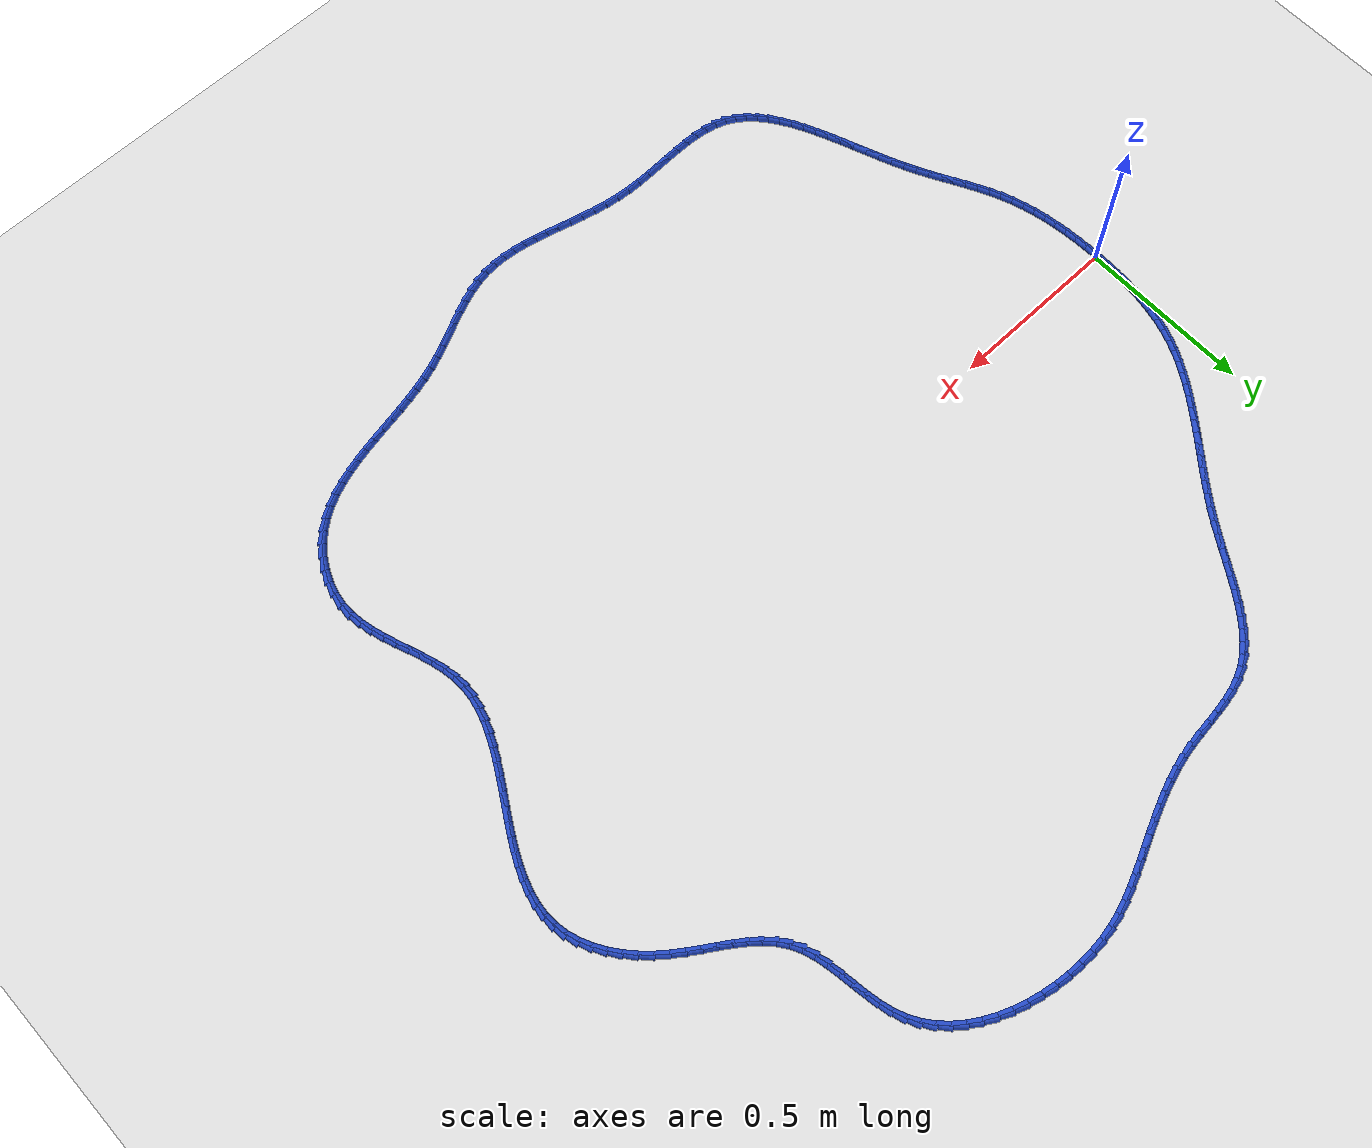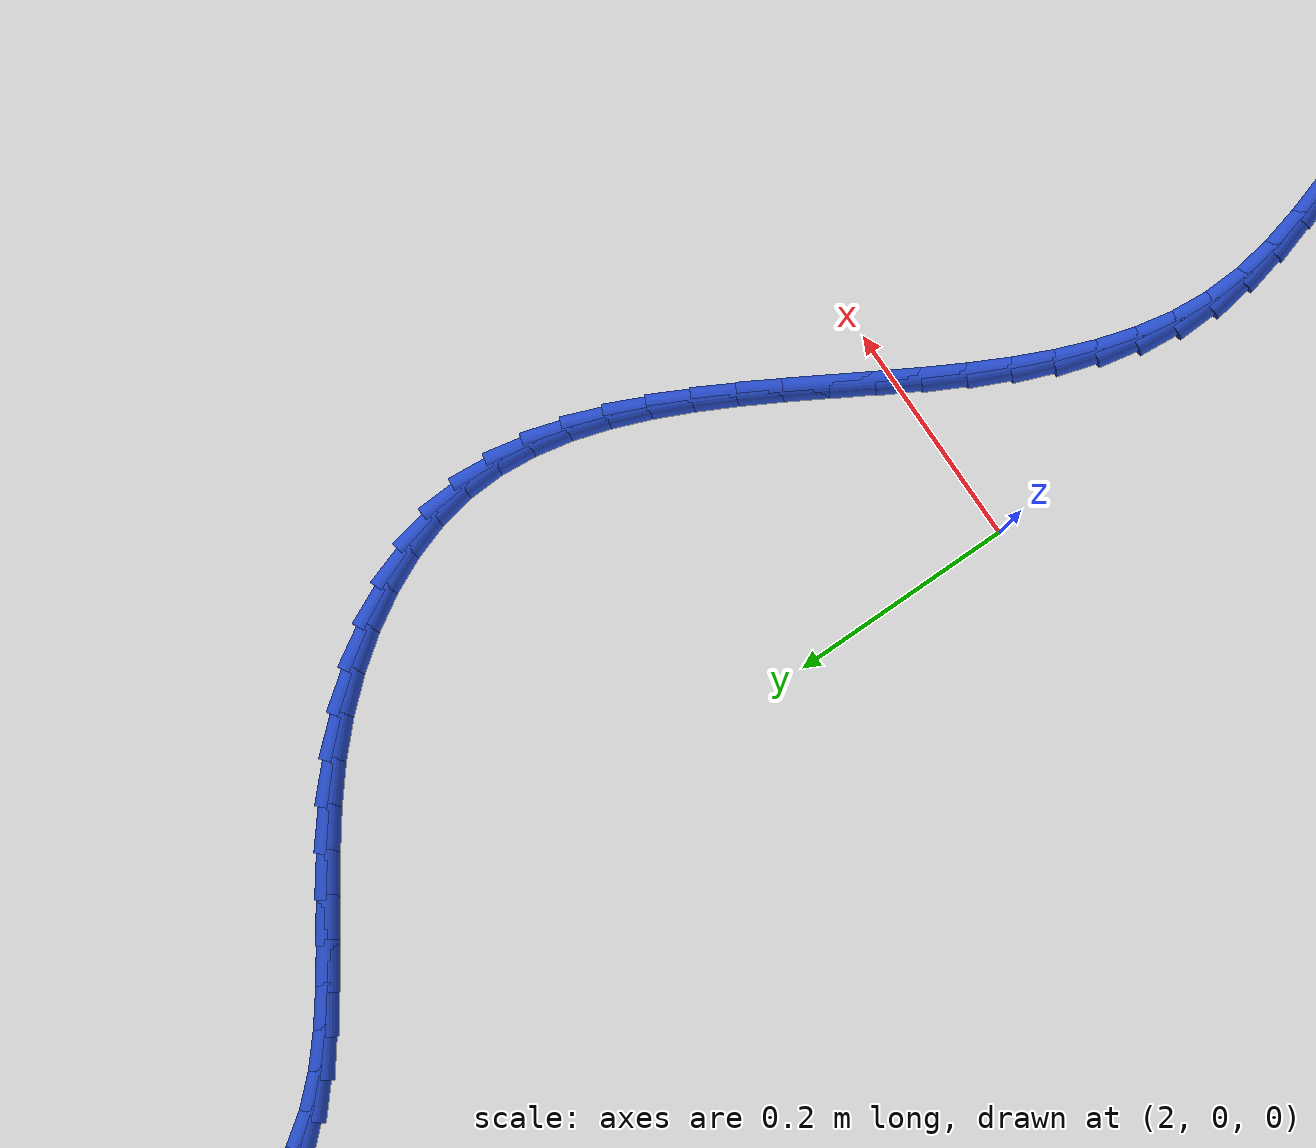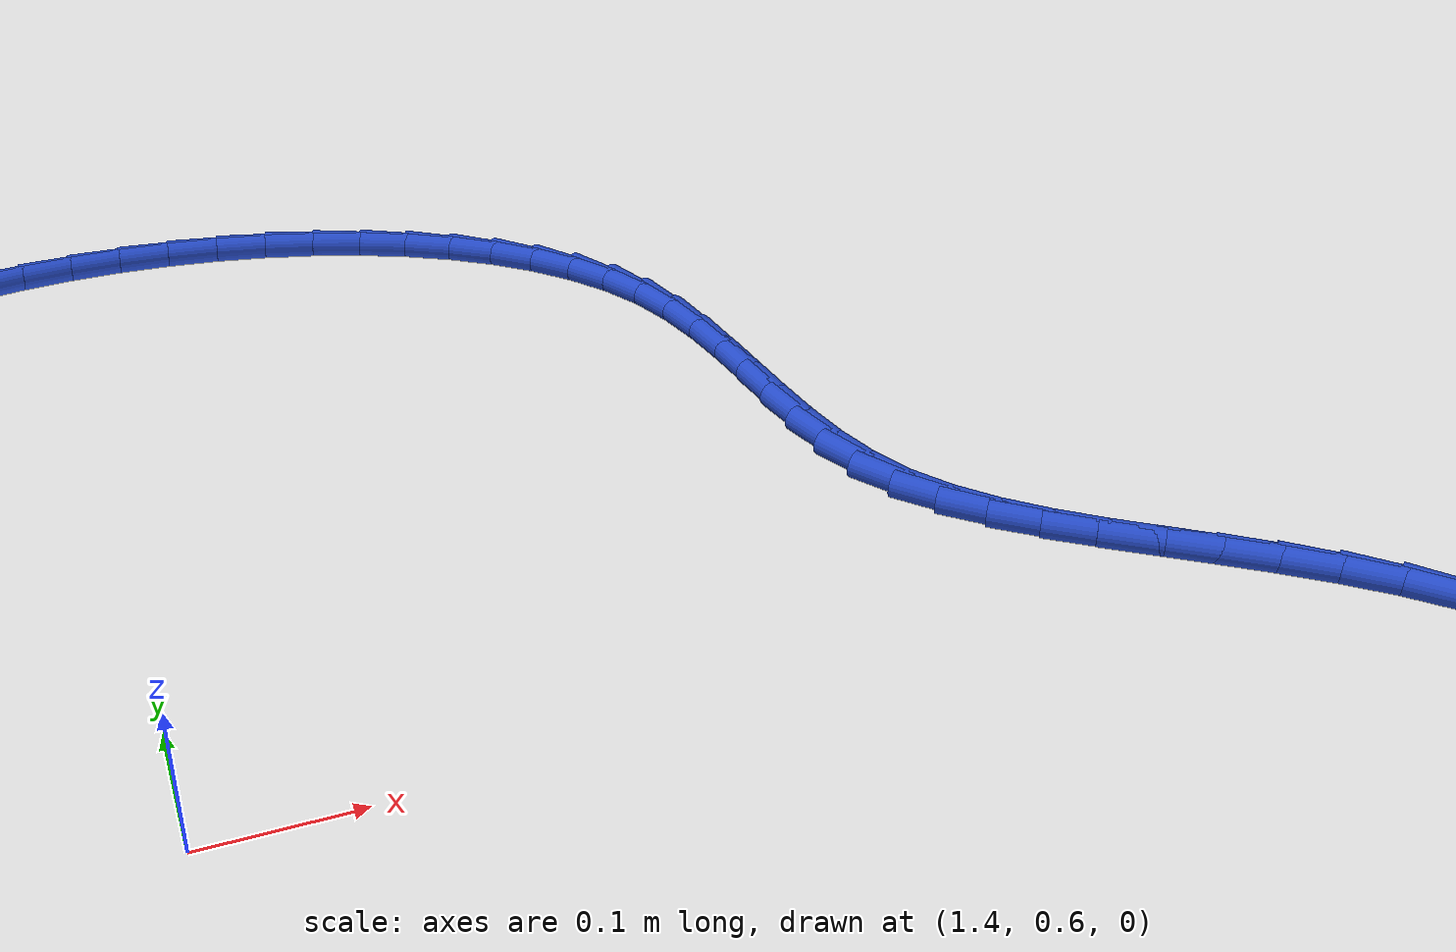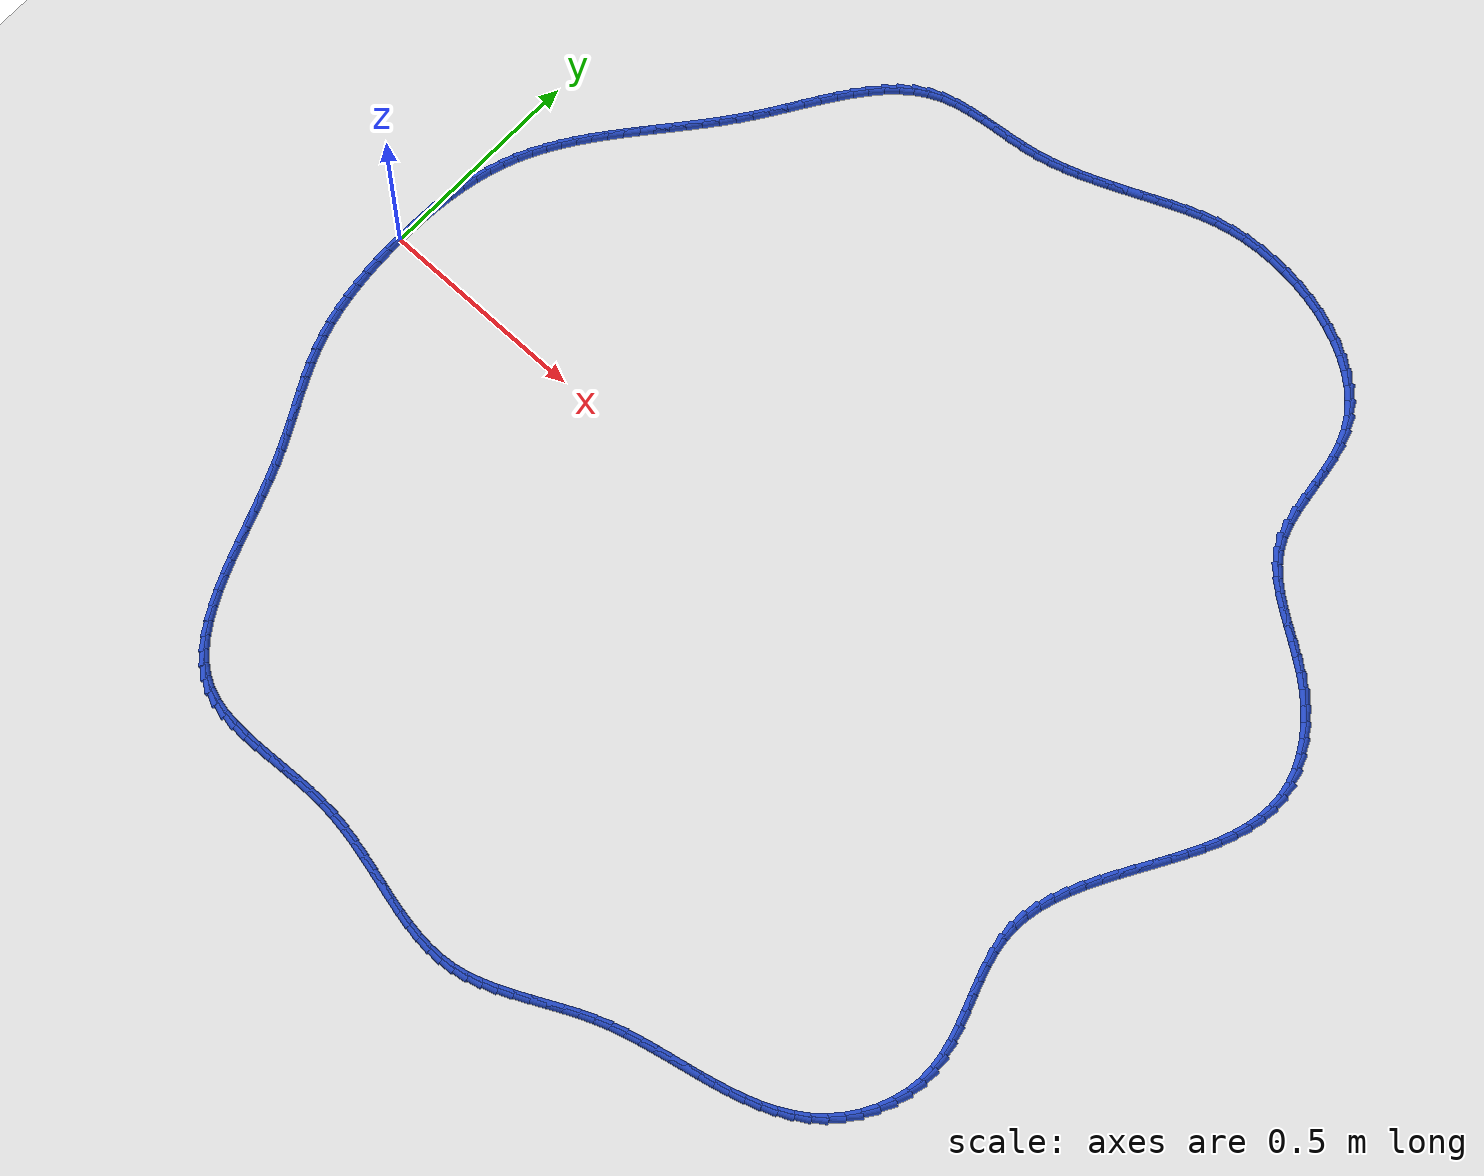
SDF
<sdf version="1.6">
 <world name="default">
  <light name="sun" type="directional">
   <pose>0 0 10 0 -0 0</pose>
   <diffuse>0.8 0.8 0.8 1</diffuse>
   <specular>0.2 0.2 0.2 1</specular>
   <attenuation>
    <range>1000</range>
    <constant>0.9</constant>
    <linear>0.01</linear>
    <quadratic>0.001</quadratic>
   </attenuation>
   <direction>-0.5 0.1 -0.9</direction>
  </light>
  <model name="ground_plane">
   <static>1</static>
   <link name="link">
    <collision name="collision">
     <geometry><plane><normal>0 0 1</normal><size>100 100</size></plane></geometry>
     <surface><friction><ode><mu>100</mu><mu2>50</mu2></ode></friction></surface>
    </collision>
    <visual name="visual">
     <cast_shadows>0</cast_shadows>
     <geometry><plane><normal>0 0 1</normal><size>100 100</size></plane></geometry>
     <material>
      <script><uri>file://media/materials/scripts/gazebo.material</uri><name>Gazebo/WhiteGlow</name></script>
     </material>
    </visual>
   </link>
  </model>
  <gravity>0 0 -9.8</gravity>
  <magnetic_field>6e-06 2.3e-05 -4.2e-05</magnetic_field>
  <atmosphere type="adiabatic"/>
  <physics name="default_physics" default="0" type="ode">
   <max_step_size>0.001</max_step_size>
   <real_time_factor>1</real_time_factor>
   <real_time_update_rate>1000</real_time_update_rate>
  </physics>
  <scene><ambient>0.4 0.4 0.4 1</ambient><background>0.7 0.7 0.7 1</background><shadows>1</shadows></scene>
  <spherical_coordinates>
   <surface_model>EARTH_WGS84</surface_model>
   <latitude_deg>0</latitude_deg>
   <longitude_deg>0</longitude_deg>
   <elevation>0</elevation>
   <heading_deg>0</heading_deg>
  </spherical_coordinates>
  <model name="line">
   <link name="link_0">
    <pose>1.9081958235744878e-17 2.0816681711721685e-17 0.01 0 1.57 1.560972597169636</pose>
    <collision name="collision">
     <geometry><cylinder><radius>0.01</radius><length>0.08</length></cylinder></geometry>
    </collision>
    <visual name="visual">
     <material>
      <script><name>Gazebo/Blue</name><uri>file://media/materials/scripts/gazebo.material</uri></script>
     </material>
     <geometry><cylinder><radius>0.01</radius><length>0.08</length></cylinder></geometry>
    </visual>
   </link>
   <link name="link_1">
    <pose>0.00035940747973483385 0.036584467585218716 0.01 0 1.57 1.5313753869513596</pose>
    <collision name="collision">
     <geometry><cylinder><radius>0.01</radius><length>0.08</length></cylinder></geometry>
    </collision>
    <visual name="visual">
     <material>
      <script><name>Gazebo/Blue</name><uri>file://media/materials/scripts/gazebo.material</uri></script>
     </material>
     <geometry><cylinder><radius>0.01</radius><length>0.08</length></cylinder></geometry>
    </visual>
   </link>
   <link name="link_2">
    <pose>0.0017988519238332909 0.07308026741367317 0.01 0 1.57 1.4980727001369023</pose>
    <collision name="collision">
     <geometry><cylinder><radius>0.01</radius><length>0.08</length></cylinder></geometry>
    </collision>
    <visual name="visual">
     <material>
      <script><name>Gazebo/Blue</name><uri>file://media/materials/scripts/gazebo.material</uri></script>
     </material>
     <geometry><cylinder><radius>0.01</radius><length>0.08</length></cylinder></geometry>
    </visual>
   </link>
   <link name="link_3">
    <pose>0.004441334345571314 0.1093521427943838 0.01 0 1.57 1.46073816377099</pose>
    <collision name="collision">
     <geometry><cylinder><radius>0.01</radius><length>0.08</length></cylinder></geometry>
    </collision>
    <visual name="visual">
     <material>
      <script><name>Gazebo/Blue</name><uri>file://media/materials/scripts/gazebo.material</uri></script>
     </material>
     <geometry><cylinder><radius>0.01</radius><length>0.08</length></cylinder></geometry>
    </visual>
   </link>
   <link name="link_4">
    <pose>0.008409855758224838 0.1452648370363711 0.01 0 1.57 1.4190131943721014</pose>
    <collision name="collision">
     <geometry><cylinder><radius>0.01</radius><length>0.08</length></cylinder></geometry>
    </collision>
    <visual name="visual">
     <material>
      <script><name>Gazebo/Blue</name><uri>file://media/materials/scripts/gazebo.material</uri></script>
     </material>
     <geometry><cylinder><radius>0.01</radius><length>0.08</length></cylinder></geometry>
    </visual>
   </link>
   <link name="link_5">
    <pose>0.013827417175069794 0.18068309344865557 0.01 0 1.57 1.3725194973205543</pose>
    <collision name="collision">
     <geometry><cylinder><radius>0.01</radius><length>0.08</length></cylinder></geometry>
    </collision>
    <visual name="visual">
     <material>
      <script><name>Gazebo/Blue</name><uri>file://media/materials/scripts/gazebo.material</uri></script>
     </material>
     <geometry><cylinder><radius>0.01</radius><length>0.08</length></cylinder></geometry>
    </visual>
   </link>
   <link name="link_6">
    <pose>0.020817019609382113 0.21547165534025764 0.01 0 1.57 1.3208793719418424</pose>
    <collision name="collision">
     <geometry><cylinder><radius>0.01</radius><length>0.08</length></cylinder></geometry>
    </collision>
    <visual name="visual">
     <material>
      <script><name>Gazebo/Blue</name><uri>file://media/materials/scripts/gazebo.material</uri></script>
     </material>
     <geometry><cylinder><radius>0.01</radius><length>0.08</length></cylinder></geometry>
    </visual>
   </link>
   <link name="link_7">
    <pose>0.029501664074437724 0.24949526602019778 0.01 0 1.57 1.2637466125806822</pose>
    <collision name="collision">
     <geometry><cylinder><radius>0.01</radius><length>0.08</length></cylinder></geometry>
    </collision>
    <visual name="visual">
     <material>
      <script><name>Gazebo/Blue</name><uri>file://media/materials/scripts/gazebo.material</uri></script>
     </material>
     <geometry><cylinder><radius>0.01</radius><length>0.08</length></cylinder></geometry>
    </visual>
   </link>
   <link name="link_8">
    <pose>0.04000435158351255 0.2826186687974965 0.01 0 1.57 1.2012964142819578</pose>
    <collision name="collision">
     <geometry><cylinder><radius>0.01</radius><length>0.08</length></cylinder></geometry>
    </collision>
    <visual name="visual">
     <material>
      <script><name>Gazebo/Blue</name><uri>file://media/materials/scripts/gazebo.material</uri></script>
     </material>
     <geometry><cylinder><radius>0.01</radius><length>0.08</length></cylinder></geometry>
    </visual>
   </link>
   <link name="link_9">
    <pose>0.05243583653621312 0.314717485289717 0.01 0 1.57 1.1396415072065778</pose>
    <collision name="collision">
     <geometry><cylinder><radius>0.01</radius><length>0.08</length></cylinder></geometry>
    </collision>
    <visual name="visual">
     <material>
      <script><name>Gazebo/Blue</name><uri>file://media/materials/scripts/gazebo.material</uri></script>
     </material>
     <geometry><cylinder><radius>0.01</radius><length>0.08</length></cylinder></geometry>
    </visual>
   </link>
   <link name="link_10">
    <pose>0.06674110704488123 0.34581458245648605 0.01 0 1.57 1.0837987090909402</pose>
    <collision name="collision">
     <geometry><cylinder><radius>0.01</radius><length>0.08</length></cylinder></geometry>
    </collision>
    <visual name="visual">
     <material>
      <script><name>Gazebo/Blue</name><uri>file://media/materials/scripts/gazebo.material</uri></script>
     </material>
     <geometry><cylinder><radius>0.01</radius><length>0.08</length></cylinder></geometry>
    </visual>
   </link>
   <link name="link_11">
    <pose>0.08274593172097461 0.3760387264512773 0.01 0 1.57 1.034422966369488</pose>
    <collision name="collision">
     <geometry><cylinder><radius>0.01</radius><length>0.08</length></cylinder></geometry>
    </collision>
    <visual name="visual">
     <material>
      <script><name>Gazebo/Blue</name><uri>file://media/materials/scripts/gazebo.material</uri></script>
     </material>
     <geometry><cylinder><radius>0.01</radius><length>0.08</length></cylinder></geometry>
    </visual>
   </link>
   <link name="link_12">
    <pose>0.10027346013421318 0.4055210098456968 0.01 0 1.57 0.9918226974642906</pose>
    <collision name="collision">
     <geometry><cylinder><radius>0.01</radius><length>0.08</length></cylinder></geometry>
    </collision>
    <visual name="visual">
     <material>
      <script><name>Gazebo/Blue</name><uri>file://media/materials/scripts/gazebo.material</uri></script>
     </material>
     <geometry><cylinder><radius>0.01</radius><length>0.08</length></cylinder></geometry>
    </visual>
   </link>
   <link name="link_13">
    <pose>0.11914684185431697 0.43439252521135124 0.01 0 1.57 0.9561078494160984</pose>
    <collision name="collision">
     <geometry><cylinder><radius>0.01</radius><length>0.08</length></cylinder></geometry>
    </collision>
    <visual name="visual">
     <material>
      <script><name>Gazebo/Blue</name><uri>file://media/materials/scripts/gazebo.material</uri></script>
     </material>
     <geometry><cylinder><radius>0.01</radius><length>0.08</length></cylinder></geometry>
    </visual>
   </link>
   <link name="link_14">
    <pose>0.13918922645100593 0.46278436511984716 0.01 0 1.57 0.9272474243927474</pose>
    <collision name="collision">
     <geometry><cylinder><radius>0.01</radius><length>0.08</length></cylinder></geometry>
    </collision>
    <visual name="visual">
     <material>
      <script><name>Gazebo/Blue</name><uri>file://media/materials/scripts/gazebo.material</uri></script>
     </material>
     <geometry><cylinder><radius>0.01</radius><length>0.08</length></cylinder></geometry>
    </visual>
   </link>
   <link name="link_15">
    <pose>0.16022376349399997 0.4908276221427911 0.01 0 1.57 0.9051218732307043</pose>
    <collision name="collision">
     <geometry><cylinder><radius>0.01</radius><length>0.08</length></cylinder></geometry>
    </collision>
    <visual name="visual">
     <material>
      <script><name>Gazebo/Blue</name><uri>file://media/materials/scripts/gazebo.material</uri></script>
     </material>
     <geometry><cylinder><radius>0.01</radius><length>0.08</length></cylinder></geometry>
    </visual>
   </link>
   <link name="link_16">
    <pose>0.1820736025530191 0.5186533888517892 0.01 0 1.57 0.8895653059646416</pose>
    <collision name="collision">
     <geometry><cylinder><radius>0.01</radius><length>0.08</length></cylinder></geometry>
    </collision>
    <visual name="visual">
     <material>
      <script><name>Gazebo/Blue</name><uri>file://media/materials/scripts/gazebo.material</uri></script>
     </material>
     <geometry><cylinder><radius>0.01</radius><length>0.08</length></cylinder></geometry>
    </visual>
   </link>
   <link name="link_17">
    <pose>0.20456189319778326 0.5463927578184484 0.01 0 1.57 0.8803960994645494</pose>
    <collision name="collision">
     <geometry><cylinder><radius>0.01</radius><length>0.08</length></cylinder></geometry>
    </collision>
    <visual name="visual">
     <material>
      <script><name>Gazebo/Blue</name><uri>file://media/materials/scripts/gazebo.material</uri></script>
     </material>
     <geometry><cylinder><radius>0.01</radius><length>0.08</length></cylinder></geometry>
    </visual>
   </link>
   <link name="link_18">
    <pose>0.22751178499801245 0.5741768216143752 0.01 0 1.57 0.8774365501781685</pose>
    <collision name="collision">
     <geometry><cylinder><radius>0.01</radius><length>0.08</length></cylinder></geometry>
    </collision>
    <visual name="visual">
     <material>
      <script><name>Gazebo/Blue</name><uri>file://media/materials/scripts/gazebo.material</uri></script>
     </material>
     <geometry><cylinder><radius>0.01</radius><length>0.08</length></cylinder></geometry>
    </visual>
   </link>
   <link name="link_19">
    <pose>0.2507464275234268 0.602136672811176 0.01 0 1.57 0.8805230590940539</pose>
    <collision name="collision">
     <geometry><cylinder><radius>0.01</radius><length>0.08</length></cylinder></geometry>
    </collision>
    <visual name="visual">
     <material>
      <script><name>Gazebo/Blue</name><uri>file://media/materials/scripts/gazebo.material</uri></script>
     </material>
     <geometry><cylinder><radius>0.01</radius><length>0.08</length></cylinder></geometry>
    </visual>
   </link>
   <link name="link_20">
    <pose>0.27408897034374585 0.6304034039804571 0.01 0 1.57 0.8895084305679589</pose>
    <collision name="collision">
     <geometry><cylinder><radius>0.01</radius><length>0.08</length></cylinder></geometry>
    </collision>
    <visual name="visual">
     <material>
      <script><name>Gazebo/Blue</name><uri>file://media/materials/scripts/gazebo.material</uri></script>
     </material>
     <geometry><cylinder><radius>0.01</radius><length>0.08</length></cylinder></geometry>
    </visual>
   </link>
   <link name="link_21">
    <pose>0.2973625630286899 0.6591081076938254 0.01 0 1.57 0.9042576268937171</pose>
    <collision name="collision">
     <geometry><cylinder><radius>0.01</radius><length>0.08</length></cylinder></geometry>
    </collision>
    <visual name="visual">
     <material>
      <script><name>Gazebo/Blue</name><uri>file://media/materials/scripts/gazebo.material</uri></script>
     </material>
     <geometry><cylinder><radius>0.01</radius><length>0.08</length></cylinder></geometry>
    </visual>
   </link>
   <link name="link_22">
    <pose>0.3203903551479789 0.6883818765228871 0.01 0 1.57 0.9246380299493415</pose>
    <collision name="collision">
     <geometry><cylinder><radius>0.01</radius><length>0.08</length></cylinder></geometry>
    </collision>
    <visual name="visual">
     <material>
      <script><name>Gazebo/Blue</name><uri>file://media/materials/scripts/gazebo.material</uri></script>
     </material>
     <geometry><cylinder><radius>0.01</radius><length>0.08</length></cylinder></geometry>
    </visual>
   </link>
   <link name="link_23">
    <pose>0.34299549627133263 0.7183558030392487 0.01 0 1.57 0.9505050984474731</pose>
    <collision name="collision">
     <geometry><cylinder><radius>0.01</radius><length>0.08</length></cylinder></geometry>
    </collision>
    <visual name="visual">
     <material>
      <script><name>Gazebo/Blue</name><uri>file://media/materials/scripts/gazebo.material</uri></script>
     </material>
     <geometry><cylinder><radius>0.01</radius><length>0.08</length></cylinder></geometry>
    </visual>
   </link>
   <link name="link_24">
    <pose>0.3650011359684713 0.7491609798145169 0.01 0 1.57 0.9790572160227771</pose>
    <collision name="collision">
     <geometry><cylinder><radius>0.01</radius><length>0.08</length></cylinder></geometry>
    </collision>
    <visual name="visual">
     <material>
      <script><name>Gazebo/Blue</name><uri>file://media/materials/scripts/gazebo.material</uri></script>
     </material>
     <geometry><cylinder><radius>0.01</radius><length>0.08</length></cylinder></geometry>
    </visual>
   </link>
   <link name="link_25">
    <pose>0.3862955159926791 0.7808453984605214 0.01 0 1.57 0.9984779983182205</pose>
    <collision name="collision">
     <geometry><cylinder><radius>0.01</radius><length>0.08</length></cylinder></geometry>
    </collision>
    <visual name="visual">
     <material>
      <script><name>Gazebo/Blue</name><uri>file://media/materials/scripts/gazebo.material</uri></script>
     </material>
     <geometry><cylinder><radius>0.01</radius><length>0.08</length></cylinder></geometry>
    </visual>
   </link>
   <link name="link_26">
    <pose>0.4070623572586121 0.8130798224710698 0.01 0 1.57 1.0057940690727885</pose>
    <collision name="collision">
     <geometry><cylinder><radius>0.01</radius><length>0.08</length></cylinder></geometry>
    </collision>
    <visual name="visual">
     <material>
      <script><name>Gazebo/Blue</name><uri>file://media/materials/scripts/gazebo.material</uri></script>
     </material>
     <geometry><cylinder><radius>0.01</radius><length>0.08</length></cylinder></geometry>
    </visual>
   </link>
   <link name="link_27">
    <pose>0.42756918036161845 0.8454280311597936 0.01 0 1.57 1.001088027684111</pose>
    <collision name="collision">
     <geometry><cylinder><radius>0.01</radius><length>0.08</length></cylinder></geometry>
    </collision>
    <visual name="visual">
     <material>
      <script><name>Gazebo/Blue</name><uri>file://media/materials/scripts/gazebo.material</uri></script>
     </material>
     <geometry><cylinder><radius>0.01</radius><length>0.08</length></cylinder></geometry>
    </visual>
   </link>
   <link name="link_28">
    <pose>0.4480835114326422 0.87745379677322 0.01 0 1.57 0.9840205954440453</pose>
    <collision name="collision">
     <geometry><cylinder><radius>0.01</radius><length>0.08</length></cylinder></geometry>
    </collision>
    <visual name="visual">
     <material>
      <script><name>Gazebo/Blue</name><uri>file://media/materials/scripts/gazebo.material</uri></script>
     </material>
     <geometry><cylinder><radius>0.01</radius><length>0.08</length></cylinder></geometry>
    </visual>
   </link>
   <link name="link_29">
    <pose>0.4688728766026268 0.9087208915578743 0.01 0 1.57 0.9538180072738426</pose>
    <collision name="collision">
     <geometry><cylinder><radius>0.01</radius><length>0.08</length></cylinder></geometry>
    </collision>
    <visual name="visual">
     <material>
      <script><name>Gazebo/Blue</name><uri>file://media/materials/scripts/gazebo.material</uri></script>
     </material>
     <geometry><cylinder><radius>0.01</radius><length>0.08</length></cylinder></geometry>
    </visual>
   </link>
   <link name="link_30">
    <pose>0.49020480200251626 0.938793087760284 0.01 0 1.57 0.9092893292387213</pose>
    <collision name="collision">
     <geometry><cylinder><radius>0.01</radius><length>0.08</length></cylinder></geometry>
    </collision>
    <visual name="visual">
     <material>
      <script><name>Gazebo/Blue</name><uri>file://media/materials/scripts/gazebo.material</uri></script>
     </material>
     <geometry><cylinder><radius>0.01</radius><length>0.08</length></cylinder></geometry>
    </visual>
   </link>
   <link name="link_31">
    <pose>0.5123468137632543 0.9672341576269753 0.01 0 1.57 0.8489117160318093</pose>
    <collision name="collision">
     <geometry><cylinder><radius>0.01</radius><length>0.08</length></cylinder></geometry>
    </collision>
    <visual name="visual">
     <material>
      <script><name>Gazebo/Blue</name><uri>file://media/materials/scripts/gazebo.material</uri></script>
     </material>
     <geometry><cylinder><radius>0.01</radius><length>0.08</length></cylinder></geometry>
    </visual>
   </link>
   <link name="link_32">
    <pose>0.5355664380157849 0.9936078734044744 0.01 0 1.57 0.7710576492510185</pose>
    <collision name="collision">
     <geometry><cylinder><radius>0.01</radius><length>0.08</length></cylinder></geometry>
    </collision>
    <visual name="visual">
     <material>
      <script><name>Gazebo/Blue</name><uri>file://media/materials/scripts/gazebo.material</uri></script>
     </material>
     <geometry><cylinder><radius>0.01</radius><length>0.08</length></cylinder></geometry>
    </visual>
   </link>
   <link name="link_33">
    <pose>0.5601312008910515 1.0174780073393082 0.01 0 1.57 0.674470268702453</pose>
    <collision name="collision">
     <geometry><cylinder><radius>0.01</radius><length>0.08</length></cylinder></geometry>
    </collision>
    <visual name="visual">
     <material>
      <script><name>Gazebo/Blue</name><uri>file://media/materials/scripts/gazebo.material</uri></script>
     </material>
     <geometry><cylinder><radius>0.01</radius><length>0.08</length></cylinder></geometry>
    </visual>
   </link>
   <link name="link_34">
    <pose>0.5863086285199981 1.0384083316780028 0.01 0 1.57 0.5590675670114021</pose>
    <collision name="collision">
     <geometry><cylinder><radius>0.01</radius><length>0.08</length></cylinder></geometry>
    </collision>
    <visual name="visual">
     <material>
      <script><name>Gazebo/Blue</name><uri>file://media/materials/scripts/gazebo.material</uri></script>
     </material>
     <geometry><cylinder><radius>0.01</radius><length>0.08</length></cylinder></geometry>
    </visual>
   </link>
   <link name="link_35">
    <pose>0.6143662470335687 1.055962618667085 0.01 0 1.57 0.42720990839506334</pose>
    <collision name="collision">
     <geometry><cylinder><radius>0.01</radius><length>0.08</length></cylinder></geometry>
    </collision>
    <visual name="visual">
     <material>
      <script><name>Gazebo/Blue</name><uri>file://media/materials/scripts/gazebo.material</uri></script>
     </material>
     <geometry><cylinder><radius>0.01</radius><length>0.08</length></cylinder></geometry>
    </visual>
   </link>
   <link name="link_36">
    <pose>0.644567732208844 1.0697117961601972 0.01 0 1.57 0.2996946086009204</pose>
    <collision name="collision">
     <geometry><cylinder><radius>0.01</radius><length>0.08</length></cylinder></geometry>
    </collision>
    <visual name="visual">
     <material>
      <script><name>Gazebo/Blue</name><uri>file://media/materials/scripts/gazebo.material</uri></script>
     </material>
     <geometry><cylinder><radius>0.01</radius><length>0.08</length></cylinder></geometry>
    </visual>
   </link>
   <link name="link_37">
    <pose>0.6769178135032915 1.0797080252154 0.01 0 1.57 0.2046014269525854</pose>
    <collision name="collision">
     <geometry><cylinder><radius>0.01</radius><length>0.08</length></cylinder></geometry>
    </collision>
    <visual name="visual">
     <material>
      <script><name>Gazebo/Blue</name><uri>file://media/materials/scripts/gazebo.material</uri></script>
     </material>
     <geometry><cylinder><radius>0.01</radius><length>0.08</length></cylinder></geometry>
    </visual>
   </link>
   <link name="link_38">
    <pose>0.7110029158059558 1.0867808559966627 0.01 0 1.57 0.14181475765033555</pose>
    <collision name="collision">
     <geometry><cylinder><radius>0.01</radius><length>0.08</length></cylinder></geometry>
    </collision>
    <visual name="visual">
     <material>
      <script><name>Gazebo/Blue</name><uri>file://media/materials/scripts/gazebo.material</uri></script>
     </material>
     <geometry><cylinder><radius>0.01</radius><length>0.08</length></cylinder></geometry>
    </visual>
   </link>
   <link name="link_39">
    <pose>0.7463714256791582 1.091830530176089 0.01 0 1.57 0.10805063357847144</pose>
    <collision name="collision">
     <geometry><cylinder><radius>0.01</radius><length>0.08</length></cylinder></geometry>
    </collision>
    <visual name="visual">
     <material>
      <script><name>Gazebo/Blue</name><uri>file://media/materials/scripts/gazebo.material</uri></script>
     </material>
     <geometry><cylinder><radius>0.01</radius><length>0.08</length></cylinder></geometry>
    </visual>
   </link>
   <link name="link_40">
    <pose>0.7825717296852219 1.0957572894257843 0.01 0 1.57 0.100914562779345</pose>
    <collision name="collision">
     <geometry><cylinder><radius>0.01</radius><length>0.08</length></cylinder></geometry>
    </collision>
    <visual name="visual">
     <material>
      <script><name>Gazebo/Blue</name><uri>file://media/materials/scripts/gazebo.material</uri></script>
     </material>
     <geometry><cylinder><radius>0.01</radius><length>0.08</length></cylinder></geometry>
    </visual>
   </link>
   <link name="link_41">
    <pose>0.8191522143864688 1.0994613754178508 0.01 0 1.57 0.1194442675543675</pose>
    <collision name="collision">
     <geometry><cylinder><radius>0.01</radius><length>0.08</length></cylinder></geometry>
    </collision>
    <visual name="visual">
     <material>
      <script><name>Gazebo/Blue</name><uri>file://media/materials/scripts/gazebo.material</uri></script>
     </material>
     <geometry><cylinder><radius>0.01</radius><length>0.08</length></cylinder></geometry>
    </visual>
   </link>
   <link name="link_42">
    <pose>0.8556612663452208 1.1038430298243942 0.01 0 1.57 0.16401281167441317</pose>
    <collision name="collision">
     <geometry><cylinder><radius>0.01</radius><length>0.08</length></cylinder></geometry>
    </collision>
    <visual name="visual">
     <material>
      <script><name>Gazebo/Blue</name><uri>file://media/materials/scripts/gazebo.material</uri></script>
     </material>
     <geometry><cylinder><radius>0.01</radius><length>0.08</length></cylinder></geometry>
    </visual>
   </link>
   <link name="link_43">
    <pose>0.8916489024307759 1.1097989645073283 0.01 0 1.57 0.22446744807597416</pose>
    <collision name="collision">
     <geometry><cylinder><radius>0.01</radius><length>0.08</length></cylinder></geometry>
    </collision>
    <visual name="visual">
     <material>
      <script><name>Gazebo/Blue</name><uri>file://media/materials/scripts/gazebo.material</uri></script>
     </material>
     <geometry><cylinder><radius>0.01</radius><length>0.08</length></cylinder></geometry>
    </visual>
   </link>
   <link name="link_44">
    <pose>0.9268457147240168 1.117834924331884 0.01 0 1.57 0.2791058630290151</pose>
    <collision name="collision">
     <geometry><cylinder><radius>0.01</radius><length>0.08</length></cylinder></geometry>
    </collision>
    <visual name="visual">
     <material>
      <script><name>Gazebo/Blue</name><uri>file://media/materials/scripts/gazebo.material</uri></script>
     </material>
     <geometry><cylinder><radius>0.01</radius><length>0.08</length></cylinder></geometry>
    </visual>
   </link>
   <link name="link_45">
    <pose>0.9613243617698087 1.1277160392310677 0.01 0 1.57 0.32489434794419864</pose>
    <collision name="collision">
     <geometry><cylinder><radius>0.01</radius><length>0.08</length></cylinder></geometry>
    </collision>
    <visual name="visual">
     <material>
      <script><name>Gazebo/Blue</name><uri>file://media/materials/scripts/gazebo.material</uri></script>
     </material>
     <geometry><cylinder><radius>0.01</radius><length>0.08</length></cylinder></geometry>
    </visual>
   </link>
   <link name="link_46">
    <pose>0.995195624142882 1.139124900369732 0.01 0 1.57 0.3614920028607713</pose>
    <collision name="collision">
     <geometry><cylinder><radius>0.01</radius><length>0.08</length></cylinder></geometry>
    </collision>
    <visual name="visual">
     <material>
      <script><name>Gazebo/Blue</name><uri>file://media/materials/scripts/gazebo.material</uri></script>
     </material>
     <geometry><cylinder><radius>0.01</radius><length>0.08</length></cylinder></geometry>
    </visual>
   </link>
   <link name="link_47">
    <pose>1.0285702824179659 1.1517440989127286 0.01 0 1.57 0.3887521610513202</pose>
    <collision name="collision">
     <geometry><cylinder><radius>0.01</radius><length>0.08</length></cylinder></geometry>
    </collision>
    <visual name="visual">
     <material>
      <script><name>Gazebo/Blue</name><uri>file://media/materials/scripts/gazebo.material</uri></script>
     </material>
     <geometry><cylinder><radius>0.01</radius><length>0.08</length></cylinder></geometry>
    </visual>
   </link>
   <link name="link_48">
    <pose>1.0615591171697907 1.1652562260249106 0.01 0 1.57 0.4066323781026633</pose>
    <collision name="collision">
     <geometry><cylinder><radius>0.01</radius><length>0.08</length></cylinder></geometry>
    </collision>
    <visual name="visual">
     <material>
      <script><name>Gazebo/Blue</name><uri>file://media/materials/scripts/gazebo.material</uri></script>
     </material>
     <geometry><cylinder><radius>0.01</radius><length>0.08</length></cylinder></geometry>
    </visual>
   </link>
   <link name="link_49">
    <pose>1.0942729089730856 1.1793438728711303 0.01 0 1.57 0.4151235438506848</pose>
    <collision name="collision">
     <geometry><cylinder><radius>0.01</radius><length>0.08</length></cylinder></geometry>
    </collision>
    <visual name="visual">
     <material>
      <script><name>Gazebo/Blue</name><uri>file://media/materials/scripts/gazebo.material</uri></script>
     </material>
     <geometry><cylinder><radius>0.01</radius><length>0.08</length></cylinder></geometry>
    </visual>
   </link>
   <link name="link_50">
    <pose>1.1268224384025802 1.1936896306162392 0.01 0 1.57 0.41420258081959976</pose>
    <collision name="collision">
     <geometry><cylinder><radius>0.01</radius><length>0.08</length></cylinder></geometry>
    </collision>
    <visual name="visual">
     <material>
      <script><name>Gazebo/Blue</name><uri>file://media/materials/scripts/gazebo.material</uri></script>
     </material>
     <geometry><cylinder><radius>0.01</radius><length>0.08</length></cylinder></geometry>
    </visual>
   </link>
   <link name="link_51">
    <pose>1.1593184860330048 1.2079760904250902 0.01 0 1.57 0.40380957212478696</pose>
    <collision name="collision">
     <geometry><cylinder><radius>0.01</radius><length>0.08</length></cylinder></geometry>
    </collision>
    <visual name="visual">
     <material>
      <script><name>Gazebo/Blue</name><uri>file://media/materials/scripts/gazebo.material</uri></script>
     </material>
     <geometry><cylinder><radius>0.01</radius><length>0.08</length></cylinder></geometry>
    </visual>
   </link>
   <link name="link_52">
    <pose>1.1918718324390887 1.2218858434625355 0.01 0 1.57 0.3836914871860909</pose>
    <collision name="collision">
     <geometry><cylinder><radius>0.01</radius><length>0.08</length></cylinder></geometry>
    </collision>
    <visual name="visual">
     <material>
      <script><name>Gazebo/Blue</name><uri>file://media/materials/scripts/gazebo.material</uri></script>
     </material>
     <geometry><cylinder><radius>0.01</radius><length>0.08</length></cylinder></geometry>
    </visual>
   </link>
   <link name="link_53">
    <pose>1.2245988064444147 1.2350977049819623 0.01 0 1.57 0.3495733230367328</pose>
    <collision name="collision">
     <geometry><cylinder><radius>0.01</radius><length>0.08</length></cylinder></geometry>
    </collision>
    <visual name="visual">
     <material>
      <script><name>Gazebo/Blue</name><uri>file://media/materials/scripts/gazebo.material</uri></script>
     </material>
     <geometry><cylinder><radius>0.01</radius><length>0.08</length></cylinder></geometry>
    </visual>
   </link>
   <link name="link_54">
    <pose>1.2577656042512653 1.2471884966224733 0.01 0 1.57 0.2974967296565237</pose>
    <collision name="collision">
     <geometry><cylinder><radius>0.01</radius><length>0.08</length></cylinder></geometry>
    </collision>
    <visual name="visual">
     <material>
      <script><name>Gazebo/Blue</name><uri>file://media/materials/scripts/gazebo.material</uri></script>
     </material>
     <geometry><cylinder><radius>0.01</radius><length>0.08</length></cylinder></geometry>
    </visual>
   </link>
   <link name="link_55">
    <pose>1.2918018086473622 1.2576238457891824 0.01 0 1.57 0.22904844200211005</pose>
    <collision name="collision">
     <geometry><cylinder><radius>0.01</radius><length>0.08</length></cylinder></geometry>
    </collision>
    <visual name="visual">
     <material>
      <script><name>Gazebo/Blue</name><uri>file://media/materials/scripts/gazebo.material</uri></script>
     </material>
     <geometry><cylinder><radius>0.01</radius><length>0.08</length></cylinder></geometry>
    </visual>
   </link>
   <link name="link_56">
    <pose>1.3271452004262887 1.2658637992096087 0.01 0 1.57 0.1510803030677481</pose>
    <collision name="collision">
     <geometry><cylinder><radius>0.01</radius><length>0.08</length></cylinder></geometry>
    </collision>
    <visual name="visual">
     <material>
      <script><name>Gazebo/Blue</name><uri>file://media/materials/scripts/gazebo.material</uri></script>
     </material>
     <geometry><cylinder><radius>0.01</radius><length>0.08</length></cylinder></geometry>
    </visual>
   </link>
   <link name="link_57">
    <pose>1.3640583111892282 1.2714834651498395 0.01 0 1.57 0.07689461572539699</pose>
    <collision name="collision">
     <geometry><cylinder><radius>0.01</radius><length>0.08</length></cylinder></geometry>
    </collision>
    <visual name="visual">
     <material>
      <script><name>Gazebo/Blue</name><uri>file://media/materials/scripts/gazebo.material</uri></script>
     </material>
     <geometry><cylinder><radius>0.01</radius><length>0.08</length></cylinder></geometry>
    </visual>
   </link>
   <link name="link_58">
    <pose>1.4022438232430807 1.2744255263011737 0.01 0 1.57 0.007180154449528899</pose>
    <collision name="collision">
     <geometry><cylinder><radius>0.01</radius><length>0.08</length></cylinder></geometry>
    </collision>
    <visual name="visual">
     <material>
      <script><name>Gazebo/Blue</name><uri>file://media/materials/scripts/gazebo.material</uri></script>
     </material>
     <geometry><cylinder><radius>0.01</radius><length>0.08</length></cylinder></geometry>
    </visual>
   </link>
   <link name="link_59">
    <pose>1.4412928617822782 1.2747059092473525 0.01 0 1.57 -0.059805752222324815</pose>
    <collision name="collision">
     <geometry><cylinder><radius>0.01</radius><length>0.08</length></cylinder></geometry>
    </collision>
    <visual name="visual">
     <material>
      <script><name>Gazebo/Blue</name><uri>file://media/materials/scripts/gazebo.material</uri></script>
     </material>
     <geometry><cylinder><radius>0.01</radius><length>0.08</length></cylinder></geometry>
    </visual>
   </link>
   <link name="link_60">
    <pose>1.480796552001252 1.2723405405721167 0.01 0 1.57 -0.12563717878167194</pose>
    <collision name="collision">
     <geometry><cylinder><radius>0.01</radius><length>0.08</length></cylinder></geometry>
    </collision>
    <visual name="visual">
     <material>
      <script><name>Gazebo/Blue</name><uri>file://media/materials/scripts/gazebo.material</uri></script>
     </material>
     <geometry><cylinder><radius>0.01</radius><length>0.08</length></cylinder></geometry>
    </visual>
   </link>
   <link name="link_61">
    <pose>1.5203460190944327 1.2673453468592069 0.01 0 1.57 -0.19179031704078175</pose>
    <collision name="collision">
     <geometry><cylinder><radius>0.01</radius><length>0.08</length></cylinder></geometry>
    </collision>
    <visual name="visual">
     <material>
      <script><name>Gazebo/Blue</name><uri>file://media/materials/scripts/gazebo.material</uri></script>
     </material>
     <geometry><cylinder><radius>0.01</radius><length>0.08</length></cylinder></geometry>
    </visual>
   </link>
   <link name="link_62">
    <pose>1.559532388256252 1.2597362546923647 0.01 0 1.57 -0.25970841203757067</pose>
    <collision name="collision">
     <geometry><cylinder><radius>0.01</radius><length>0.08</length></cylinder></geometry>
    </collision>
    <visual name="visual">
     <material>
      <script><name>Gazebo/Blue</name><uri>file://media/materials/scripts/gazebo.material</uri></script>
     </material>
     <geometry><cylinder><radius>0.01</radius><length>0.08</length></cylinder></geometry>
    </visual>
   </link>
   <link name="link_63">
    <pose>1.5979467846811415 1.24952919065533 0.01 0 1.57 -0.33085771131666547</pose>
    <collision name="collision">
     <geometry><cylinder><radius>0.01</radius><length>0.08</length></cylinder></geometry>
    </collision>
    <visual name="visual">
     <material>
      <script><name>Gazebo/Blue</name><uri>file://media/materials/scripts/gazebo.material</uri></script>
     </material>
     <geometry><cylinder><radius>0.01</radius><length>0.08</length></cylinder></geometry>
    </visual>
   </link>
   <link name="link_64">
    <pose>1.6351803335635327 1.2367400813318457 0.01 0 1.57 -0.4067698905890832</pose>
    <collision name="collision">
     <geometry><cylinder><radius>0.01</radius><length>0.08</length></cylinder></geometry>
    </collision>
    <visual name="visual">
     <material>
      <script><name>Gazebo/Blue</name><uri>file://media/materials/scripts/gazebo.material</uri></script>
     </material>
     <geometry><cylinder><radius>0.01</radius><length>0.08</length></cylinder></geometry>
    </visual>
   </link>
   <link name="link_65">
    <pose>1.670824160097856 1.2213848533056508 0.01 0 1.57 -0.4890613343130064</pose>
    <collision name="collision">
     <geometry><cylinder><radius>0.01</radius><length>0.08</length></cylinder></geometry>
    </collision>
    <visual name="visual">
     <material>
      <script><name>Gazebo/Blue</name><uri>file://media/materials/scripts/gazebo.material</uri></script>
     </material>
     <geometry><cylinder><radius>0.01</radius><length>0.08</length></cylinder></geometry>
    </visual>
   </link>
   <link name="link_66">
    <pose>1.7044693894785439 1.203479433160487 0.01 0 1.57 -0.5794105340813437</pose>
    <collision name="collision">
     <geometry><cylinder><radius>0.01</radius><length>0.08</length></cylinder></geometry>
    </collision>
    <visual name="visual">
     <material>
      <script><name>Gazebo/Blue</name><uri>file://media/materials/scripts/gazebo.material</uri></script>
     </material>
     <geometry><cylinder><radius>0.01</radius><length>0.08</length></cylinder></geometry>
    </visual>
   </link>
   <link name="link_67">
    <pose>1.735707146900027 1.1830397474800958 0.01 0 1.57 -0.6794621371061317</pose>
    <collision name="collision">
     <geometry><cylinder><radius>0.01</radius><length>0.08</length></cylinder></geometry>
    </collision>
    <visual name="visual">
     <material>
      <script><name>Gazebo/Blue</name><uri>file://media/materials/scripts/gazebo.material</uri></script>
     </material>
     <geometry><cylinder><radius>0.01</radius><length>0.08</length></cylinder></geometry>
    </visual>
   </link>
   <link name="link_68">
    <pose>1.7641285575567367 1.1600817228482179 0.01 0 1.57 -0.7906145691643144</pose>
    <collision name="collision">
     <geometry><cylinder><radius>0.01</radius><length>0.08</length></cylinder></geometry>
    </collision>
    <visual name="visual">
     <material>
      <script><name>Gazebo/Blue</name><uri>file://media/materials/scripts/gazebo.material</uri></script>
     </material>
     <geometry><cylinder><radius>0.01</radius><length>0.08</length></cylinder></geometry>
    </visual>
   </link>
   <link name="link_69">
    <pose>1.789324746643105 1.1346212858485933 0.01 0 1.57 -0.9136532449403916</pose>
    <collision name="collision">
     <geometry><cylinder><radius>0.01</radius><length>0.08</length></cylinder></geometry>
    </collision>
    <visual name="visual">
     <material>
      <script><name>Gazebo/Blue</name><uri>file://media/materials/scripts/gazebo.material</uri></script>
     </material>
     <geometry><cylinder><radius>0.01</radius><length>0.08</length></cylinder></geometry>
    </visual>
   </link>
   <link name="link_70">
    <pose>1.8108868393535629 1.1066743630649645 0.01 0 1.57 -1.048244124482746</pose>
    <collision name="collision">
     <geometry><cylinder><radius>0.01</radius><length>0.08</length></cylinder></geometry>
    </collision>
    <visual name="visual">
     <material>
      <script><name>Gazebo/Blue</name><uri>file://media/materials/scripts/gazebo.material</uri></script>
     </material>
     <geometry><cylinder><radius>0.01</radius><length>0.08</length></cylinder></geometry>
    </visual>
   </link>
   <link name="link_71">
    <pose>1.8284059608825411 1.0762568810810713 0.01 0 1.57 -1.1879264139602956</pose>
    <collision name="collision">
     <geometry><cylinder><radius>0.01</radius><length>0.08</length></cylinder></geometry>
    </collision>
    <visual name="visual">
     <material>
      <script><name>Gazebo/Blue</name><uri>file://media/materials/scripts/gazebo.material</uri></script>
     </material>
     <geometry><cylinder><radius>0.01</radius><length>0.08</length></cylinder></geometry>
    </visual>
   </link>
   <link name="link_72">
    <pose>1.8416197596820878 1.0434474812581143 0.01 0 1.57 -1.3008192775604723</pose>
    <collision name="collision">
     <geometry><cylinder><radius>0.01</radius><length>0.08</length></cylinder></geometry>
    </collision>
    <visual name="visual">
     <material>
      <script><name>Gazebo/Blue</name><uri>file://media/materials/scripts/gazebo.material</uri></script>
     </material>
     <geometry><cylinder><radius>0.01</radius><length>0.08</length></cylinder></geometry>
    </visual>
   </link>
   <link name="link_73">
    <pose>1.851225691722106 1.0087356210684364 0.01 0 1.57 -1.3763448915019312</pose>
    <collision name="collision">
     <geometry><cylinder><radius>0.01</radius><length>0.08</length></cylinder></geometry>
    </collision>
    <visual name="visual">
     <material>
      <script><name>Gazebo/Blue</name><uri>file://media/materials/scripts/gazebo.material</uri></script>
     </material>
     <geometry><cylinder><radius>0.01</radius><length>0.08</length></cylinder></geometry>
    </visual>
   </link>
   <link name="link_74">
    <pose>1.858307552627886 0.9727761188008506 0.01 0 1.57 -1.4176318183195047</pose>
    <collision name="collision">
     <geometry><cylinder><radius>0.01</radius><length>0.08</length></cylinder></geometry>
    </collision>
    <visual name="visual">
     <material>
      <script><name>Gazebo/Blue</name><uri>file://media/materials/scripts/gazebo.material</uri></script>
     </material>
     <geometry><cylinder><radius>0.01</radius><length>0.08</length></cylinder></geometry>
    </visual>
   </link>
   <link name="link_75">
    <pose>1.8639501957796238 0.9362242454836501 0.01 0 1.57 -1.4268702929997736</pose>
    <collision name="collision">
     <geometry><cylinder><radius>0.01</radius><length>0.08</length></cylinder></geometry>
    </collision>
    <visual name="visual">
     <material>
      <script><name>Gazebo/Blue</name><uri>file://media/materials/scripts/gazebo.material</uri></script>
     </material>
     <geometry><cylinder><radius>0.01</radius><length>0.08</length></cylinder></geometry>
    </visual>
   </link>
   <link name="link_76">
    <pose>1.8692384745575144 0.8997352721451277 0.01 0 1.57 -1.4040985261394905</pose>
    <collision name="collision">
     <geometry><cylinder><radius>0.01</radius><length>0.08</length></cylinder></geometry>
    </collision>
    <visual name="visual">
     <material>
      <script><name>Gazebo/Blue</name><uri>file://media/materials/scripts/gazebo.material</uri></script>
     </material>
     <geometry><cylinder><radius>0.01</radius><length>0.08</length></cylinder></geometry>
    </visual>
   </link>
   <link name="link_77">
    <pose>1.8752572423417517 0.8639644698135764 0.01 0 1.57 -1.3468628635485378</pose>
    <collision name="collision">
     <geometry><cylinder><radius>0.01</radius><length>0.08</length></cylinder></geometry>
    </collision>
    <visual name="visual">
     <material>
      <script><name>Gazebo/Blue</name><uri>file://media/materials/scripts/gazebo.material</uri></script>
     </material>
     <geometry><cylinder><radius>0.01</radius><length>0.08</length></cylinder></geometry>
    </visual>
   </link>
   <link name="link_78">
    <pose>1.8830913525125301 0.8295671095172884 0.01 0 1.57 -1.2505825760809968</pose>
    <collision name="collision">
     <geometry><cylinder><radius>0.01</radius><length>0.08</length></cylinder></geometry>
    </collision>
    <visual name="visual">
     <material>
      <script><name>Gazebo/Blue</name><uri>file://media/materials/scripts/gazebo.material</uri></script>
     </material>
     <geometry><cylinder><radius>0.01</radius><length>0.08</length></cylinder></geometry>
    </visual>
   </link>
   <link name="link_79">
    <pose>1.8938256584500455 0.7971984622845566 0.01 0 1.57 -1.1108161293282333</pose>
    <collision name="collision">
     <geometry><cylinder><radius>0.01</radius><length>0.08</length></cylinder></geometry>
    </collision>
    <visual name="visual">
     <material>
      <script><name>Gazebo/Blue</name><uri>file://media/materials/scripts/gazebo.material</uri></script>
     </material>
     <geometry><cylinder><radius>0.01</radius><length>0.08</length></cylinder></geometry>
    </visual>
   </link>
   <link name="link_80">
    <pose>1.9085354161791954 0.767507218855628 0.01 0 1.57 -0.9514670862350821</pose>
    <collision name="collision">
     <geometry><cylinder><radius>0.01</radius><length>0.08</length></cylinder></geometry>
    </collision>
    <visual name="visual">
     <material>
      <script><name>Gazebo/Blue</name><uri>file://media/materials/scripts/gazebo.material</uri></script>
     </material>
     <geometry><cylinder><radius>0.01</radius><length>0.08</length></cylinder></geometry>
    </visual>
   </link>
   <link name="link_81">
    <pose>1.9276478150879193 0.7406977324410486 0.01 0 1.57 -0.8180963661991288</pose>
    <collision name="collision">
     <geometry><cylinder><radius>0.01</radius><length>0.08</length></cylinder></geometry>
    </collision>
    <visual name="visual">
     <material>
      <script><name>Gazebo/Blue</name><uri>file://media/materials/scripts/gazebo.material</uri></script>
     </material>
     <geometry><cylinder><radius>0.01</radius><length>0.08</length></cylinder></geometry>
    </visual>
   </link>
   <link name="link_82">
    <pose>1.9505416517551404 0.7162555408636425 0.01 0 1.57 -0.7175437458545639</pose>
    <collision name="collision">
     <geometry><cylinder><radius>0.01</radius><length>0.08</length></cylinder></geometry>
    </collision>
    <visual name="visual">
     <material>
      <script><name>Gazebo/Blue</name><uri>file://media/materials/scripts/gazebo.material</uri></script>
     </material>
     <geometry><cylinder><radius>0.01</radius><length>0.08</length></cylinder></geometry>
    </visual>
   </link>
   <link name="link_83">
    <pose>1.9765002062303925 0.6936006924173899 0.01 0 1.57 -0.6484015484913899</pose>
    <collision name="collision">
     <geometry><cylinder><radius>0.01</radius><length>0.08</length></cylinder></geometry>
    </collision>
    <visual name="visual">
     <material>
      <script><name>Gazebo/Blue</name><uri>file://media/materials/scripts/gazebo.material</uri></script>
     </material>
     <geometry><cylinder><radius>0.01</radius><length>0.08</length></cylinder></geometry>
    </visual>
   </link>
   <link name="link_84">
    <pose>2.004806758563208 0.67215323539627 0.01 0 1.57 -0.6076601861337262</pose>
    <collision name="collision">
     <geometry><cylinder><radius>0.01</radius><length>0.08</length></cylinder></geometry>
    </collision>
    <visual name="visual">
     <material>
      <script><name>Gazebo/Blue</name><uri>file://media/materials/scripts/gazebo.material</uri></script>
     </material>
     <geometry><cylinder><radius>0.01</radius><length>0.08</length></cylinder></geometry>
    </visual>
   </link>
   <link name="link_85">
    <pose>2.0347445888031235 0.6513332180942628 0.01 0 1.57 -0.5925723056267691</pose>
    <collision name="collision">
     <geometry><cylinder><radius>0.01</radius><length>0.08</length></cylinder></geometry>
    </collision>
    <visual name="visual">
     <material>
      <script><name>Gazebo/Blue</name><uri>file://media/materials/scripts/gazebo.material</uri></script>
     </material>
     <geometry><cylinder><radius>0.01</radius><length>0.08</length></cylinder></geometry>
    </visual>
   </link>
   <link name="link_86">
    <pose>2.06559697699967 0.6305606888053478 0.01 0 1.57 -0.6013674357572023</pose>
    <collision name="collision">
     <geometry><cylinder><radius>0.01</radius><length>0.08</length></cylinder></geometry>
    </collision>
    <visual name="visual">
     <material>
      <script><name>Gazebo/Blue</name><uri>file://media/materials/scripts/gazebo.material</uri></script>
     </material>
     <geometry><cylinder><radius>0.01</radius><length>0.08</length></cylinder></geometry>
    </visual>
   </link>
   <link name="link_87">
    <pose>2.0966472032023815 0.6092556958235048 0.01 0 1.57 -0.6333397539335717</pose>
    <collision name="collision">
     <geometry><cylinder><radius>0.01</radius><length>0.08</length></cylinder></geometry>
    </collision>
    <visual name="visual">
     <material>
      <script><name>Gazebo/Blue</name><uri>file://media/materials/scripts/gazebo.material</uri></script>
     </material>
     <geometry><cylinder><radius>0.01</radius><length>0.08</length></cylinder></geometry>
    </visual>
   </link>
   <link name="link_88">
    <pose>2.1271785474607925 0.5868382874427128 0.01 0 1.57 -0.688596215068687</pose>
    <collision name="collision">
     <geometry><cylinder><radius>0.01</radius><length>0.08</length></cylinder></geometry>
    </collision>
    <visual name="visual">
     <material>
      <script><name>Gazebo/Blue</name><uri>file://media/materials/scripts/gazebo.material</uri></script>
     </material>
     <geometry><cylinder><radius>0.01</radius><length>0.08</length></cylinder></geometry>
    </visual>
   </link>
   <link name="link_89">
    <pose>2.1564742898244362 0.5627285119569525 0.01 0 1.57 -0.7649621310855835</pose>
    <collision name="collision">
     <geometry><cylinder><radius>0.01</radius><length>0.08</length></cylinder></geometry>
    </collision>
    <visual name="visual">
     <material>
      <script><name>Gazebo/Blue</name><uri>file://media/materials/scripts/gazebo.material</uri></script>
     </material>
     <geometry><cylinder><radius>0.01</radius><length>0.08</length></cylinder></geometry>
    </visual>
   </link>
   <link name="link_90">
    <pose>2.183848967723012 0.5364504361298772 0.01 0 1.57 -0.8485032546470809</pose>
    <collision name="collision">
     <geometry><cylinder><radius>0.01</radius><length>0.08</length></cylinder></geometry>
    </collision>
    <visual name="visual">
     <material>
      <script><name>Gazebo/Blue</name><uri>file://media/materials/scripts/gazebo.material</uri></script>
     </material>
     <geometry><cylinder><radius>0.01</radius><length>0.08</length></cylinder></geometry>
    </visual>
   </link>
   <link name="link_91">
    <pose>2.208799267518622 0.5081342828745077 0.01 0 1.57 -0.9362140040301882</pose>
    <collision name="collision">
     <geometry><cylinder><radius>0.01</radius><length>0.08</length></cylinder></geometry>
    </collision>
    <visual name="visual">
     <material>
      <script><name>Gazebo/Blue</name><uri>file://media/materials/scripts/gazebo.material</uri></script>
     </material>
     <geometry><cylinder><radius>0.01</radius><length>0.08</length></cylinder></geometry>
    </visual>
   </link>
   <link name="link_92">
    <pose>2.2308876754935523 0.47812924441498517 0.01 0 1.57 -1.030789057519459</pose>
    <collision name="collision">
     <geometry><cylinder><radius>0.01</radius><length>0.08</length></cylinder></geometry>
    </collision>
    <visual name="visual">
     <material>
      <script><name>Gazebo/Blue</name><uri>file://media/materials/scripts/gazebo.material</uri></script>
     </material>
     <geometry><cylinder><radius>0.01</radius><length>0.08</length></cylinder></geometry>
    </visual>
   </link>
   <link name="link_93">
    <pose>2.249676767366114 0.44678481060111047 0.01 0 1.57 -1.135109411028016</pose>
    <collision name="collision">
     <geometry><cylinder><radius>0.01</radius><length>0.08</length></cylinder></geometry>
    </collision>
    <visual name="visual">
     <material>
      <script><name>Gazebo/Blue</name><uri>file://media/materials/scripts/gazebo.material</uri></script>
     </material>
     <geometry><cylinder><radius>0.01</radius><length>0.08</length></cylinder></geometry>
    </visual>
   </link>
   <link name="link_94">
    <pose>2.2647291188546195 0.4144504712826833 0.01 0 1.57 -1.2521440039129987</pose>
    <collision name="collision">
     <geometry><cylinder><radius>0.01</radius><length>0.08</length></cylinder></geometry>
    </collision>
    <visual name="visual">
     <material>
      <script><name>Gazebo/Blue</name><uri>file://media/materials/scripts/gazebo.material</uri></script>
     </material>
     <geometry><cylinder><radius>0.01</radius><length>0.08</length></cylinder></geometry>
    </visual>
   </link>
   <link name="link_95">
    <pose>2.27560730567738 0.3814757163095041 0.01 0 1.57 -1.3845808456315494</pose>
    <collision name="collision">
     <geometry><cylinder><radius>0.01</radius><length>0.08</length></cylinder></geometry>
    </collision>
    <visual name="visual">
     <material>
      <script><name>Gazebo/Blue</name><uri>file://media/materials/scripts/gazebo.material</uri></script>
     </material>
     <geometry><cylinder><radius>0.01</radius><length>0.08</length></cylinder></geometry>
    </visual>
   </link>
   <link name="link_96">
    <pose>2.2818745440784545 0.34820979774798516 0.01 0 1.57 -1.5268475022962134</pose>
    <collision name="collision">
     <geometry><cylinder><radius>0.01</radius><length>0.08</length></cylinder></geometry>
    </collision>
    <visual name="visual">
     <material>
      <script><name>Gazebo/Blue</name><uri>file://media/materials/scripts/gazebo.material</uri></script>
     </material>
     <geometry><cylinder><radius>0.01</radius><length>0.08</length></cylinder></geometry>
    </visual>
   </link>
   <link name="link_97">
    <pose>2.283338927330215 0.31491106157744253 0.01 0 1.57 1.4834201986905355</pose>
    <collision name="collision">
     <geometry><cylinder><radius>0.01</radius><length>0.08</length></cylinder></geometry>
    </collision>
    <visual name="visual">
     <material>
      <script><name>Gazebo/Blue</name><uri>file://media/materials/scripts/gazebo.material</uri></script>
     </material>
     <geometry><cylinder><radius>0.01</radius><length>0.08</length></cylinder></geometry>
    </visual>
   </link>
   <link name="link_98">
    <pose>2.2804217991483062 0.28161019584376645 0.01 0 1.57 1.3698992429816483</pose>
    <collision name="collision">
     <geometry><cylinder><radius>0.01</radius><length>0.08</length></cylinder></geometry>
    </collision>
    <visual name="visual">
     <material>
      <script><name>Gazebo/Blue</name><uri>file://media/materials/scripts/gazebo.material</uri></script>
     </material>
     <geometry><cylinder><radius>0.01</radius><length>0.08</length></cylinder></geometry>
    </visual>
   </link>
   <link name="link_99">
    <pose>2.273638948387314 0.24830282757432248 0.01 0 1.57 1.27556291092709</pose>
    <collision name="collision">
     <geometry><cylinder><radius>0.01</radius><length>0.08</length></cylinder></geometry>
    </collision>
    <visual name="visual">
     <material>
      <script><name>Gazebo/Blue</name><uri>file://media/materials/scripts/gazebo.material</uri></script>
     </material>
     <geometry><cylinder><radius>0.01</radius><length>0.08</length></cylinder></geometry>
    </visual>
   </link>
   <link name="link_100">
    <pose>2.2635061639018264 0.214984583796475 0.01 0 1.57 1.19980329290685</pose>
    <collision name="collision">
     <geometry><cylinder><radius>0.01</radius><length>0.08</length></cylinder></geometry>
    </collision>
    <visual name="visual">
     <material>
      <script><name>Gazebo/Blue</name><uri>file://media/materials/scripts/gazebo.material</uri></script>
     </material>
     <geometry><cylinder><radius>0.01</radius><length>0.08</length></cylinder></geometry>
    </visual>
   </link>
   <link name="link_101">
    <pose>2.250539234546428 0.1816510915375882 0.01 0 1.57 1.141072661619232</pose>
    <collision name="collision">
     <geometry><cylinder><radius>0.01</radius><length>0.08</length></cylinder></geometry>
    </collision>
    <visual name="visual">
     <material>
      <script><name>Gazebo/Blue</name><uri>file://media/materials/scripts/gazebo.material</uri></script>
     </material>
     <geometry><cylinder><radius>0.01</radius><length>0.08</length></cylinder></geometry>
    </visual>
   </link>
   <link name="link_102">
    <pose>2.235253949175705 0.14829797782502765 0.01 0 1.57 1.0976239912985797</pose>
    <collision name="collision">
     <geometry><cylinder><radius>0.01</radius><length>0.08</length></cylinder></geometry>
    </collision>
    <visual name="visual">
     <material>
      <script><name>Gazebo/Blue</name><uri>file://media/materials/scripts/gazebo.material</uri></script>
     </material>
     <geometry><cylinder><radius>0.01</radius><length>0.08</length></cylinder></geometry>
    </visual>
   </link>
   <link name="link_103">
    <pose>2.2181660966442434 0.11492086968615756 0.01 0 1.57 1.0679159006255938</pose>
    <collision name="collision">
     <geometry><cylinder><radius>0.01</radius><length>0.08</length></cylinder></geometry>
    </collision>
    <visual name="visual">
     <material>
      <script><name>Gazebo/Blue</name><uri>file://media/materials/scripts/gazebo.material</uri></script>
     </material>
     <geometry><cylinder><radius>0.01</radius><length>0.08</length></cylinder></geometry>
    </visual>
   </link>
   <link name="link_104">
    <pose>2.199791465806629 0.08151539414834261 0.01 0 1.57 1.0507924036710552</pose>
    <collision name="collision">
     <geometry><cylinder><radius>0.01</radius><length>0.08</length></cylinder></geometry>
    </collision>
    <visual name="visual">
     <material>
      <script><name>Gazebo/Blue</name><uri>file://media/materials/scripts/gazebo.material</uri></script>
     </material>
     <geometry><cylinder><radius>0.01</radius><length>0.08</length></cylinder></geometry>
    </visual>
   </link>
   <link name="link_105">
    <pose>2.1806458455174482 0.048077178238947624 0.01 0 1.57 1.0455449904310146</pose>
    <collision name="collision">
     <geometry><cylinder><radius>0.01</radius><length>0.08</length></cylinder></geometry>
    </collision>
    <visual name="visual">
     <material>
      <script><name>Gazebo/Blue</name><uri>file://media/materials/scripts/gazebo.material</uri></script>
     </material>
     <geometry><cylinder><radius>0.01</radius><length>0.08</length></cylinder></geometry>
    </visual>
   </link>
   <link name="link_106">
    <pose>2.1612450246312873 0.014601848985336383 0.01 0 1.57 1.0519254045728823</pose>
    <collision name="collision">
     <geometry><cylinder><radius>0.01</radius><length>0.08</length></cylinder></geometry>
    </collision>
    <visual name="visual">
     <material>
      <script><name>Gazebo/Blue</name><uri>file://media/materials/scripts/gazebo.material</uri></script>
     </material>
     <geometry><cylinder><radius>0.01</radius><length>0.08</length></cylinder></geometry>
    </visual>
   </link>
   <link name="link_107">
    <pose>2.142104792002731 -0.018914966585124746 0.01 0 1.57 1.0701429780346505</pose>
    <collision name="collision">
     <geometry><cylinder><radius>0.01</radius><length>0.08</length></cylinder></geometry>
    </collision>
    <visual name="visual">
     <material>
      <script><name>Gazebo/Blue</name><uri>file://media/materials/scripts/gazebo.material</uri></script>
     </material>
     <geometry><cylinder><radius>0.01</radius><length>0.08</length></cylinder></geometry>
    </visual>
   </link>
   <link name="link_108">
    <pose>2.1237409364863673 -0.05247764144507192 0.01 0 1.57 1.100855945752654</pose>
    <collision name="collision">
     <geometry><cylinder><radius>0.01</radius><length>0.08</length></cylinder></geometry>
    </collision>
    <visual name="visual">
     <material>
      <script><name>Gazebo/Blue</name><uri>file://media/materials/scripts/gazebo.material</uri></script>
     </material>
     <geometry><cylinder><radius>0.01</radius><length>0.08</length></cylinder></geometry>
    </visual>
   </link>
   <link name="link_109">
    <pose>2.106669246936781 -0.08609054856714045 0.01 0 1.57 1.1451460386002406</pose>
    <collision name="collision">
     <geometry><cylinder><radius>0.01</radius><length>0.08</length></cylinder></geometry>
    </collision>
    <visual name="visual">
     <material>
      <script><name>Gazebo/Blue</name><uri>file://media/materials/scripts/gazebo.material</uri></script>
     </material>
     <geometry><cylinder><radius>0.01</radius><length>0.08</length></cylinder></geometry>
    </visual>
   </link>
   <link name="link_110">
    <pose>2.091405512208558 -0.11975806092396561 0.01 0 1.57 1.2044424744856452</pose>
    <collision name="collision">
     <geometry><cylinder><radius>0.01</radius><length>0.08</length></cylinder></geometry>
    </collision>
    <visual name="visual">
     <material>
      <script><name>Gazebo/Blue</name><uri>file://media/materials/scripts/gazebo.material</uri></script>
     </material>
     <geometry><cylinder><radius>0.01</radius><length>0.08</length></cylinder></geometry>
    </visual>
   </link>
   <link name="link_111">
    <pose>2.0784655211562852 -0.1534845514881827 0.01 0 1.57 1.2803306787076154</pose>
    <collision name="collision">
     <geometry><cylinder><radius>0.01</radius><length>0.08</length></cylinder></geometry>
    </collision>
    <visual name="visual">
     <material>
      <script><name>Gazebo/Blue</name><uri>file://media/materials/scripts/gazebo.material</uri></script>
     </material>
     <geometry><cylinder><radius>0.01</radius><length>0.08</length></cylinder></geometry>
    </visual>
   </link>
   <link name="link_112">
    <pose>2.0683650626345473 -0.1872743932324278 0.01 0 1.57 1.3741499458725963</pose>
    <collision name="collision">
     <geometry><cylinder><radius>0.01</radius><length>0.08</length></cylinder></geometry>
    </collision>
    <visual name="visual">
     <material>
      <script><name>Gazebo/Blue</name><uri>file://media/materials/scripts/gazebo.material</uri></script>
     </material>
     <geometry><cylinder><radius>0.01</radius><length>0.08</length></cylinder></geometry>
    </visual>
   </link>
   <link name="link_113">
    <pose>2.061619925497931 -0.2211319591293347 0.01 0 1.57 1.4862926106542302</pose>
    <collision name="collision">
     <geometry><cylinder><radius>0.01</radius><length>0.08</length></cylinder></geometry>
    </collision>
    <visual name="visual">
     <material>
      <script><name>Gazebo/Blue</name><uri>file://media/materials/scripts/gazebo.material</uri></script>
     </material>
     <geometry><cylinder><radius>0.01</radius><length>0.08</length></cylinder></geometry>
    </visual>
   </link>
   <link name="link_114">
    <pose>2.058745898601023 -0.2550616221515395 0.01 0 1.57 -1.527681448363805</pose>
    <collision name="collision">
     <geometry><cylinder><radius>0.01</radius><length>0.08</length></cylinder></geometry>
    </collision>
    <visual name="visual">
     <material>
      <script><name>Gazebo/Blue</name><uri>file://media/materials/scripts/gazebo.material</uri></script>
     </material>
     <geometry><cylinder><radius>0.01</radius><length>0.08</length></cylinder></geometry>
    </visual>
   </link>
   <link name="link_115">
    <pose>2.0602129889022796 -0.28906800666263005 0.01 0 1.57 -1.410283058895095</pose>
    <collision name="collision">
     <geometry><cylinder><radius>0.01</radius><length>0.08</length></cylinder></geometry>
    </collision>
    <visual name="visual">
     <material>
      <script><name>Gazebo/Blue</name><uri>file://media/materials/scripts/gazebo.material</uri></script>
     </material>
     <geometry><cylinder><radius>0.01</radius><length>0.08</length></cylinder></geometry>
    </visual>
   </link>
   <link name="link_116">
    <pose>2.0657326760879715 -0.323159902141878 0.01 0 1.57 -1.3227255762940087</pose>
    <collision name="collision">
     <geometry><cylinder><radius>0.01</radius><length>0.08</length></cylinder></geometry>
    </collision>
    <visual name="visual">
     <material>
      <script><name>Gazebo/Blue</name><uri>file://media/materials/scripts/gazebo.material</uri></script>
     </material>
     <geometry><cylinder><radius>0.01</radius><length>0.08</length></cylinder></geometry>
    </visual>
   </link>
   <link name="link_117">
    <pose>2.0743924934856635 -0.35734952419291416 0.01 0 1.57 -1.2639245569333988</pose>
    <collision name="collision">
     <geometry><cylinder><radius>0.01</radius><length>0.08</length></cylinder></geometry>
    </collision>
    <visual name="visual">
     <material>
      <script><name>Gazebo/Blue</name><uri>file://media/materials/scripts/gazebo.material</uri></script>
     </material>
     <geometry><cylinder><radius>0.01</radius><length>0.08</length></cylinder></geometry>
    </visual>
   </link>
   <link name="link_118">
    <pose>2.0852614309942177 -0.3916491902423733 0.01 0 1.57 -1.2315528829271254</pose>
    <collision name="collision">
     <geometry><cylinder><radius>0.01</radius><length>0.08</length></cylinder></geometry>
    </collision>
    <visual name="visual">
     <material>
      <script><name>Gazebo/Blue</name><uri>file://media/materials/scripts/gazebo.material</uri></script>
     </material>
     <geometry><cylinder><radius>0.01</radius><length>0.08</length></cylinder></geometry>
    </visual>
   </link>
   <link name="link_119">
    <pose>2.0974084785124987 -0.42607121771689144 0.01 0 1.57 -1.2238649001833684</pose>
    <collision name="collision">
     <geometry><cylinder><radius>0.01</radius><length>0.08</length></cylinder></geometry>
    </collision>
    <visual name="visual">
     <material>
      <script><name>Gazebo/Blue</name><uri>file://media/materials/scripts/gazebo.material</uri></script>
     </material>
     <geometry><cylinder><radius>0.01</radius><length>0.08</length></cylinder></geometry>
    </visual>
   </link>
   <link name="link_120">
    <pose>2.1099026259393696 -0.46062792404310193 0.01 0 1.57 -1.2401941057059491</pose>
    <collision name="collision">
     <geometry><cylinder><radius>0.01</radius><length>0.08</length></cylinder></geometry>
    </collision>
    <visual name="visual">
     <material>
      <script><name>Gazebo/Blue</name><uri>file://media/materials/scripts/gazebo.material</uri></script>
     </material>
     <geometry><cylinder><radius>0.01</radius><length>0.08</length></cylinder></geometry>
    </visual>
   </link>
   <link name="link_121">
    <pose>2.121812863173695 -0.4953316266476406 0.01 0 1.57 -1.2810137080686268</pose>
    <collision name="collision">
     <geometry><cylinder><radius>0.01</radius><length>0.08</length></cylinder></geometry>
    </collision>
    <visual name="visual">
     <material>
      <script><name>Gazebo/Blue</name><uri>file://media/materials/scripts/gazebo.material</uri></script>
     </material>
     <geometry><cylinder><radius>0.01</radius><length>0.08</length></cylinder></geometry>
    </visual>
   </link>
   <link name="link_122">
    <pose>2.1322081801143375 -0.5301946429571426 0.01 0 1.57 -1.3476734948573184</pose>
    <collision name="collision">
     <geometry><cylinder><radius>0.01</radius><length>0.08</length></cylinder></geometry>
    </collision>
    <visual name="visual">
     <material>
      <script><name>Gazebo/Blue</name><uri>file://media/materials/scripts/gazebo.material</uri></script>
     </material>
     <geometry><cylinder><radius>0.01</radius><length>0.08</length></cylinder></geometry>
    </visual>
   </link>
   <link name="link_123">
    <pose>2.1401575666601613 -0.5652292903982427 0.01 0 1.57 -1.4416880618542678</pose>
    <collision name="collision">
     <geometry><cylinder><radius>0.01</radius><length>0.08</length></cylinder></geometry>
    </collision>
    <visual name="visual">
     <material>
      <script><name>Gazebo/Blue</name><uri>file://media/materials/scripts/gazebo.material</uri></script>
     </material>
     <geometry><cylinder><radius>0.01</radius><length>0.08</length></cylinder></geometry>
    </visual>
   </link>
   <link name="link_124">
    <pose>2.14473001271003 -0.6004478863975761 0.01 0 1.57 -1.5633274511015618</pose>
    <collision name="collision">
     <geometry><cylinder><radius>0.01</radius><length>0.08</length></cylinder></geometry>
    </collision>
    <visual name="visual">
     <material>
      <script><name>Gazebo/Blue</name><uri>file://media/materials/scripts/gazebo.material</uri></script>
     </material>
     <geometry><cylinder><radius>0.01</radius><length>0.08</length></cylinder></geometry>
    </visual>
   </link>
   <link name="link_125">
    <pose>2.144994526763749 -0.6358627394493018 0.01 0 1.57 1.4386494223326007</pose>
    <collision name="collision">
     <geometry><cylinder><radius>0.01</radius><length>0.08</length></cylinder></geometry>
    </collision>
    <visual name="visual">
     <material>
      <script><name>Gazebo/Blue</name><uri>file://media/materials/scripts/gazebo.material</uri></script>
     </material>
     <geometry><cylinder><radius>0.01</radius><length>0.08</length></cylinder></geometry>
    </visual>
   </link>
   <link name="link_126">
    <pose>2.1402757228905145 -0.6713634120660366 0.01 0 1.57 1.3066078154890457</pose>
    <collision name="collision">
     <geometry><cylinder><radius>0.01</radius><length>0.08</length></cylinder></geometry>
    </collision>
    <visual name="visual">
     <material>
      <script><name>Gazebo/Blue</name><uri>file://media/materials/scripts/gazebo.material</uri></script>
     </material>
     <geometry><cylinder><radius>0.01</radius><length>0.08</length></cylinder></geometry>
    </visual>
   </link>
   <link name="link_127">
    <pose>2.1307956187495396 -0.706408518855953 0.01 0 1.57 1.1841836093207105</pose>
    <collision name="collision">
     <geometry><cylinder><radius>0.01</radius><length>0.08</length></cylinder></geometry>
    </collision>
    <visual name="visual">
     <material>
      <script><name>Gazebo/Blue</name><uri>file://media/materials/scripts/gazebo.material</uri></script>
     </material>
     <geometry><cylinder><radius>0.01</radius><length>0.08</length></cylinder></geometry>
    </visual>
   </link>
   <link name="link_128">
    <pose>2.116973068699692 -0.7403621502196337 0.01 0 1.57 1.067436139034323</pose>
    <collision name="collision">
     <geometry><cylinder><radius>0.01</radius><length>0.08</length></cylinder></geometry>
    </collision>
    <visual name="visual">
     <material>
      <script><name>Gazebo/Blue</name><uri>file://media/materials/scripts/gazebo.material</uri></script>
     </material>
     <geometry><cylinder><radius>0.01</radius><length>0.08</length></cylinder></geometry>
    </visual>
   </link>
   <link name="link_129">
    <pose>2.099226927099838 -0.7725883965576621 0.01 0 1.57 0.9523185350801644</pose>
    <collision name="collision">
     <geometry><cylinder><radius>0.01</radius><length>0.08</length></cylinder></geometry>
    </collision>
    <visual name="visual">
     <material>
      <script><name>Gazebo/Blue</name><uri>file://media/materials/scripts/gazebo.material</uri></script>
     </material>
     <geometry><cylinder><radius>0.01</radius><length>0.08</length></cylinder></geometry>
    </visual>
   </link>
   <link name="link_130">
    <pose>2.077976048308846 -0.8024513482706205 0.01 0 1.57 0.8347128496299778</pose>
    <collision name="collision">
     <geometry><cylinder><radius>0.01</radius><length>0.08</length></cylinder></geometry>
    </collision>
    <visual name="visual">
     <material>
      <script><name>Gazebo/Blue</name><uri>file://media/materials/scripts/gazebo.material</uri></script>
     </material>
     <geometry><cylinder><radius>0.01</radius><length>0.08</length></cylinder></geometry>
    </visual>
   </link>
   <link name="link_131">
    <pose>2.053639286685581 -0.8293150957590916 0.01 0 1.57 0.7126925319178531</pose>
    <collision name="collision">
     <geometry><cylinder><radius>0.01</radius><length>0.08</length></cylinder></geometry>
    </collision>
    <visual name="visual">
     <material>
      <script><name>Gazebo/Blue</name><uri>file://media/materials/scripts/gazebo.material</uri></script>
     </material>
     <geometry><cylinder><radius>0.01</radius><length>0.08</length></cylinder></geometry>
    </visual>
   </link>
   <link name="link_132">
    <pose>2.026628858564759 -0.8526580826045804 0.01 0 1.57 0.598159795508978</pose>
    <collision name="collision">
     <geometry><cylinder><radius>0.01</radius><length>0.08</length></cylinder></geometry>
    </collision>
    <visual name="visual">
     <material>
      <script><name>Gazebo/Blue</name><uri>file://media/materials/scripts/gazebo.material</uri></script>
     </material>
     <geometry><cylinder><radius>0.01</radius><length>0.08</length></cylinder></geometry>
    </visual>
   </link>
   <link name="link_133">
    <pose>1.9973179171559567 -0.872631692485543 0.01 0 1.57 0.49821451637391667</pose>
    <collision name="collision">
     <geometry><cylinder><radius>0.01</radius><length>0.08</length></cylinder></geometry>
    </collision>
    <visual name="visual">
     <material>
      <script><name>Gazebo/Blue</name><uri>file://media/materials/scripts/gazebo.material</uri></script>
     </material>
     <geometry><cylinder><radius>0.01</radius><length>0.08</length></cylinder></geometry>
    </visual>
   </link>
   <link name="link_134">
    <pose>1.9660653739704712 -0.8896326506854739 0.01 0 1.57 0.4139422535714238</pose>
    <collision name="collision">
     <geometry><cylinder><radius>0.01</radius><length>0.08</length></cylinder></geometry>
    </collision>
    <visual name="visual">
     <material>
      <script><name>Gazebo/Blue</name><uri>file://media/materials/scripts/gazebo.material</uri></script>
     </material>
     <geometry><cylinder><radius>0.01</radius><length>0.08</length></cylinder></geometry>
    </visual>
   </link>
   <link name="link_135">
    <pose>1.9332301198075488 -0.9040580392942142 0.01 0 1.57 0.34518213589649005</pose>
    <collision name="collision">
     <geometry><cylinder><radius>0.01</radius><length>0.08</length></cylinder></geometry>
    </collision>
    <visual name="visual">
     <material>
      <script><name>Gazebo/Blue</name><uri>file://media/materials/scripts/gazebo.material</uri></script>
     </material>
     <geometry><cylinder><radius>0.01</radius><length>0.08</length></cylinder></geometry>
    </visual>
   </link>
   <link name="link_136">
    <pose>1.8991710454664352 -0.9163049404016046 0.01 0 1.57 0.29114927223493925</pose>
    <collision name="collision">
     <geometry><cylinder><radius>0.01</radius><length>0.08</length></cylinder></geometry>
    </collision>
    <visual name="visual">
     <material>
      <script><name>Gazebo/Blue</name><uri>file://media/materials/scripts/gazebo.material</uri></script>
     </material>
     <geometry><cylinder><radius>0.01</radius><length>0.08</length></cylinder></geometry>
    </visual>
   </link>
   <link name="link_137">
    <pose>1.8642470417463752 -0.9267704360974847 0.01 0 1.57 0.2509112144687305</pose>
    <collision name="collision">
     <geometry><cylinder><radius>0.01</radius><length>0.08</length></cylinder></geometry>
    </collision>
    <visual name="visual">
     <material>
      <script><name>Gazebo/Blue</name><uri>file://media/materials/scripts/gazebo.material</uri></script>
     </material>
     <geometry><cylinder><radius>0.01</radius><length>0.08</length></cylinder></geometry>
    </visual>
   </link>
   <link name="link_138">
    <pose>1.828816999446614 -0.9358516084716956 0.01 0 1.57 0.22369591817441575</pose>
    <collision name="collision">
     <geometry><cylinder><radius>0.01</radius><length>0.08</length></cylinder></geometry>
    </collision>
    <visual name="visual">
     <material>
      <script><name>Gazebo/Blue</name><uri>file://media/materials/scripts/gazebo.material</uri></script>
     </material>
     <geometry><cylinder><radius>0.01</radius><length>0.08</length></cylinder></geometry>
    </visual>
   </link>
   <link name="link_139">
    <pose>1.7932398093663982 -0.9439455396140771 0.01 0 1.57 0.20886384631039176</pose>
    <collision name="collision">
     <geometry><cylinder><radius>0.01</radius><length>0.08</length></cylinder></geometry>
    </collision>
    <visual name="visual">
     <material>
      <script><name>Gazebo/Blue</name><uri>file://media/materials/scripts/gazebo.material</uri></script>
     </material>
     <geometry><cylinder><radius>0.01</radius><length>0.08</length></cylinder></geometry>
    </visual>
   </link>
   <link name="link_140">
    <pose>1.757844983019163 -0.9514476487095401 0.01 0 1.57 0.20482359440519665</pose>
    <collision name="collision">
     <geometry><cylinder><radius>0.01</radius><length>0.08</length></cylinder></geometry>
    </collision>
    <visual name="visual">
     <material>
      <script><name>Gazebo/Blue</name><uri>file://media/materials/scripts/gazebo.material</uri></script>
     </material>
     <geometry><cylinder><radius>0.01</radius><length>0.08</length></cylinder></geometry>
    </visual>
   </link>
   <link name="link_141">
    <pose>1.7227379481323593 -0.9587406715158076 0.01 0 1.57 0.2110943246702978</pose>
    <collision name="collision">
     <geometry><cylinder><radius>0.01</radius><length>0.08</length></cylinder></geometry>
    </collision>
    <visual name="visual">
     <material>
      <script><name>Gazebo/Blue</name><uri>file://media/materials/scripts/gazebo.material</uri></script>
     </material>
     <geometry><cylinder><radius>0.01</radius><length>0.08</length></cylinder></geometry>
    </visual>
   </link>
   <link name="link_142">
    <pose>1.6879209108712943 -0.9662015013189496 0.01 0 1.57 0.22784641219477988</pose>
    <collision name="collision">
     <geometry><cylinder><radius>0.01</radius><length>0.08</length></cylinder></geometry>
    </collision>
    <visual name="visual">
     <material>
      <script><name>Gazebo/Blue</name><uri>file://media/materials/scripts/gazebo.material</uri></script>
     </material>
     <geometry><cylinder><radius>0.01</radius><length>0.08</length></cylinder></geometry>
    </visual>
   </link>
   <link name="link_143">
    <pose>1.653395527718645 -0.9742070002922989 0.01 0 1.57 0.25509826873567637</pose>
    <collision name="collision">
     <geometry><cylinder><radius>0.01</radius><length>0.08</length></cylinder></geometry>
    </collision>
    <visual name="visual">
     <material>
      <script><name>Gazebo/Blue</name><uri>file://media/materials/scripts/gazebo.material</uri></script>
     </material>
     <geometry><cylinder><radius>0.01</radius><length>0.08</length></cylinder></geometry>
    </visual>
   </link>
   <link name="link_144">
    <pose>1.6191634551570888 -0.9831340306091904 0.01 0 1.57 0.29265372695438596</pose>
    <collision name="collision">
     <geometry><cylinder><radius>0.01</radius><length>0.08</length></cylinder></geometry>
    </collision>
    <visual name="visual">
     <material>
      <script><name>Gazebo/Blue</name><uri>file://media/materials/scripts/gazebo.material</uri></script>
     </material>
     <geometry><cylinder><radius>0.01</radius><length>0.08</length></cylinder></geometry>
    </visual>
   </link>
   <link name="link_145">
    <pose>1.5852263496693022 -0.9933594544429573 0.01 0 1.57 0.3400211483701454</pose>
    <collision name="collision">
     <geometry><cylinder><radius>0.01</radius><length>0.08</length></cylinder></geometry>
    </collision>
    <visual name="visual">
     <material>
      <script><name>Gazebo/Blue</name><uri>file://media/materials/scripts/gazebo.material</uri></script>
     </material>
     <geometry><cylinder><radius>0.01</radius><length>0.08</length></cylinder></geometry>
    </visual>
   </link>
   <link name="link_146">
    <pose>1.5515858677379637 -1.0052601339669331 0.01 0 1.57 0.39305021493020154</pose>
    <collision name="collision">
     <geometry><cylinder><radius>0.01</radius><length>0.08</length></cylinder></geometry>
    </collision>
    <visual name="visual">
     <material>
      <script><name>Gazebo/Blue</name><uri>file://media/materials/scripts/gazebo.material</uri></script>
     </material>
     <geometry><cylinder><radius>0.01</radius><length>0.08</length></cylinder></geometry>
    </visual>
   </link>
   <link name="link_147">
    <pose>1.5182365175213939 -1.0190876083138467 0.01 0 1.57 0.4333604814716811</pose>
    <collision name="collision">
     <geometry><cylinder><radius>0.01</radius><length>0.08</length></cylinder></geometry>
    </collision>
    <visual name="visual">
     <material>
      <script><name>Gazebo/Blue</name><uri>file://media/materials/scripts/gazebo.material</uri></script>
     </material>
     <geometry><cylinder><radius>0.01</radius><length>0.08</length></cylinder></geometry>
    </visual>
   </link>
   <link name="link_148">
    <pose>1.48513349475592 -1.034404198834398 0.01 0 1.57 0.45571437456150743</pose>
    <collision name="collision">
     <geometry><cylinder><radius>0.01</radius><length>0.08</length></cylinder></geometry>
    </collision>
    <visual name="visual">
     <material>
      <script><name>Gazebo/Blue</name><uri>file://media/materials/scripts/gazebo.material</uri></script>
     </material>
     <geometry><cylinder><radius>0.01</radius><length>0.08</length></cylinder></geometry>
    </visual>
   </link>
   <link name="link_149">
    <pose>1.4522185523821014 -1.0505365503828266 0.01 0 1.57 0.46076390980225784</pose>
    <collision name="collision">
     <geometry><cylinder><radius>0.01</radius><length>0.08</length></cylinder></geometry>
    </collision>
    <visual name="visual">
     <material>
      <script><name>Gazebo/Blue</name><uri>file://media/materials/scripts/gazebo.material</uri></script>
     </material>
     <geometry><cylinder><radius>0.01</radius><length>0.08</length></cylinder></geometry>
    </visual>
   </link>
   <link name="link_150">
    <pose>1.4194334316323083 -1.0668111025476674 0.01 0 1.57 0.4485302625646909</pose>
    <collision name="collision">
     <geometry><cylinder><radius>0.01</radius><length>0.08</length></cylinder></geometry>
    </collision>
    <visual name="visual">
     <material>
      <script><name>Gazebo/Blue</name><uri>file://media/materials/scripts/gazebo.material</uri></script>
     </material>
     <geometry><cylinder><radius>0.01</radius><length>0.08</length></cylinder></geometry>
    </visual>
   </link>
   <link name="link_151">
    <pose>1.386719873738911 -1.0825542949174576 0.01 0 1.57 0.41834756291333625</pose>
    <collision name="collision">
     <geometry><cylinder><radius>0.01</radius><length>0.08</length></cylinder></geometry>
    </collision>
    <visual name="visual">
     <material>
      <script><name>Gazebo/Blue</name><uri>file://media/materials/scripts/gazebo.material</uri></script>
     </material>
     <geometry><cylinder><radius>0.01</radius><length>0.08</length></cylinder></geometry>
    </visual>
   </link>
   <link name="link_152">
    <pose>1.3540196199342818 -1.0970925670807312 0.01 0 1.57 0.3689146723055442</pose>
    <collision name="collision">
     <geometry><cylinder><radius>0.01</radius><length>0.08</length></cylinder></geometry>
    </collision>
    <visual name="visual">
     <material>
      <script><name>Gazebo/Blue</name><uri>file://media/materials/scripts/gazebo.material</uri></script>
     </material>
     <geometry><cylinder><radius>0.01</radius><length>0.08</length></cylinder></geometry>
    </visual>
   </link>
   <link name="link_153">
    <pose>1.3212744114507906 -1.1097523586260256 0.01 0 1.57 0.29851405369021344</pose>
    <collision name="collision">
     <geometry><cylinder><radius>0.01</radius><length>0.08</length></cylinder></geometry>
    </collision>
    <visual name="visual">
     <material>
      <script><name>Gazebo/Blue</name><uri>file://media/materials/scripts/gazebo.material</uri></script>
     </material>
     <geometry><cylinder><radius>0.01</radius><length>0.08</length></cylinder></geometry>
    </visual>
   </link>
   <link name="link_154">
    <pose>1.288425989520808 -1.1198601091418756 0.01 0 1.57 0.20554747653267536</pose>
    <collision name="collision">
     <geometry><cylinder><radius>0.01</radius><length>0.08</length></cylinder></geometry>
    </collision>
    <visual name="visual">
     <material>
      <script><name>Gazebo/Blue</name><uri>file://media/materials/scripts/gazebo.material</uri></script>
     </material>
     <geometry><cylinder><radius>0.01</radius><length>0.08</length></cylinder></geometry>
    </visual>
   </link>
   <link name="link_155">
    <pose>1.255416099480471 -1.1267424080181498 0.01 0 1.57 0.09711880539987694</pose>
    <collision name="collision">
     <geometry><cylinder><radius>0.01</radius><length>0.08</length></cylinder></geometry>
    </collision>
    <visual name="visual">
     <material>
      <script><name>Gazebo/Blue</name><uri>file://media/materials/scripts/gazebo.material</uri></script>
     </material>
     <geometry><cylinder><radius>0.01</radius><length>0.08</length></cylinder></geometry>
    </visual>
   </link>
   <link name="link_156">
    <pose>1.2221934255452087 -1.129979137171354 0.01 0 1.57 -0.0017170573194045954</pose>
    <collision name="collision">
     <geometry><cylinder><radius>0.01</radius><length>0.08</length></cylinder></geometry>
    </collision>
    <visual name="visual">
     <material>
      <script><name>Gazebo/Blue</name><uri>file://media/materials/scripts/gazebo.material</uri></script>
     </material>
     <geometry><cylinder><radius>0.01</radius><length>0.08</length></cylinder></geometry>
    </visual>
   </link>
   <link name="link_157">
    <pose>1.1887277868566062 -1.1299216746950231 0.01 0 1.57 -0.08439774060859331</pose>
    <collision name="collision">
     <geometry><cylinder><radius>0.01</radius><length>0.08</length></cylinder></geometry>
    </collision>
    <visual name="visual">
     <material>
      <script><name>Gazebo/Blue</name><uri>file://media/materials/scripts/gazebo.material</uri></script>
     </material>
     <geometry><cylinder><radius>0.01</radius><length>0.08</length></cylinder></geometry>
    </visual>
   </link>
   <link name="link_158">
    <pose>1.1549930119902592 -1.1270677565638192 0.01 0 1.57 -0.15027274336543392</pose>
    <collision name="collision">
     <geometry><cylinder><radius>0.01</radius><length>0.08</length></cylinder></geometry>
    </collision>
    <visual name="visual">
     <material>
      <script><name>Gazebo/Blue</name><uri>file://media/materials/scripts/gazebo.material</uri></script>
     </material>
     <geometry><cylinder><radius>0.01</radius><length>0.08</length></cylinder></geometry>
    </visual>
   </link>
   <link name="link_159">
    <pose>1.120962929521763 -1.1219151187524046 0.01 0 1.57 -0.19972638635487164</pose>
    <collision name="collision">
     <geometry><cylinder><radius>0.01</radius><length>0.08</length></cylinder></geometry>
    </collision>
    <visual name="visual">
     <material>
      <script><name>Gazebo/Blue</name><uri>file://media/materials/scripts/gazebo.material</uri></script>
     </material>
     <geometry><cylinder><radius>0.01</radius><length>0.08</length></cylinder></geometry>
    </visual>
   </link>
   <link name="link_160">
    <pose>1.0866113680267109 -1.11496149723544 0.01 0 1.57 -0.23361096037218496</pose>
    <collision name="collision">
     <geometry><cylinder><radius>0.01</radius><length>0.08</length></cylinder></geometry>
    </collision>
    <visual name="visual">
     <material>
      <script><name>Gazebo/Blue</name><uri>file://media/materials/scripts/gazebo.material</uri></script>
     </material>
     <geometry><cylinder><radius>0.01</radius><length>0.08</length></cylinder></geometry>
    </visual>
   </link>
   <link name="link_161">
    <pose>1.051912156080699 -1.1067046279875887 0.01 0 1.57 -0.25285566538584753</pose>
    <collision name="collision">
     <geometry><cylinder><radius>0.01</radius><length>0.08</length></cylinder></geometry>
    </collision>
    <visual name="visual">
     <material>
      <script><name>Gazebo/Blue</name><uri>file://media/materials/scripts/gazebo.material</uri></script>
     </material>
     <geometry><cylinder><radius>0.01</radius><length>0.08</length></cylinder></geometry>
    </visual>
   </link>
   <link name="link_162">
    <pose>1.0168391222593207 -1.0976422469835116 0.01 0 1.57 -0.2582501961681299</pose>
    <collision name="collision">
     <geometry><cylinder><radius>0.01</radius><length>0.08</length></cylinder></geometry>
    </collision>
    <visual name="visual">
     <material>
      <script><name>Gazebo/Blue</name><uri>file://media/materials/scripts/gazebo.material</uri></script>
     </material>
     <geometry><cylinder><radius>0.01</radius><length>0.08</length></cylinder></geometry>
    </visual>
   </link>
   <link name="link_163">
    <pose>0.9813660951381723 -1.088272090197871 0.01 0 1.57 -0.25035634954910585</pose>
    <collision name="collision">
     <geometry><cylinder><radius>0.01</radius><length>0.08</length></cylinder></geometry>
    </collision>
    <visual name="visual">
     <material>
      <script><name>Gazebo/Blue</name><uri>file://media/materials/scripts/gazebo.material</uri></script>
     </material>
     <geometry><cylinder><radius>0.01</radius><length>0.08</length></cylinder></geometry>
    </visual>
   </link>
   <link name="link_164">
    <pose>0.9454669032928469 -1.0790918936053282 0.01 0 1.57 -0.22950525379686185</pose>
    <collision name="collision">
     <geometry><cylinder><radius>0.01</radius><length>0.08</length></cylinder></geometry>
    </collision>
    <visual name="visual">
     <material>
      <script><name>Gazebo/Blue</name><uri>file://media/materials/scripts/gazebo.material</uri></script>
     </material>
     <geometry><cylinder><radius>0.01</radius><length>0.08</length></cylinder></geometry>
    </visual>
   </link>
   <link name="link_165">
    <pose>0.9091153752989414 -1.0705993931805462 0.01 0 1.57 -0.19585634455069859</pose>
    <collision name="collision">
     <geometry><cylinder><radius>0.01</radius><length>0.08</length></cylinder></geometry>
    </collision>
    <visual name="visual">
     <material>
      <script><name>Gazebo/Blue</name><uri>file://media/materials/scripts/gazebo.material</uri></script>
     </material>
     <geometry><cylinder><radius>0.01</radius><length>0.08</length></cylinder></geometry>
    </visual>
   </link>
   <link name="link_166">
    <pose>0.8722853397320489 -1.0632923248981858 0.01 0 1.57 -0.14951053516440008</pose>
    <collision name="collision">
     <geometry><cylinder><radius>0.01</radius><length>0.08</length></cylinder></geometry>
    </collision>
    <visual name="visual">
     <material>
      <script><name>Gazebo/Blue</name><uri>file://media/materials/scripts/gazebo.material</uri></script>
     </material>
     <geometry><cylinder><radius>0.01</radius><length>0.08</length></cylinder></geometry>
    </visual>
   </link>
   <link name="link_167">
    <pose>0.8349506251677654 -1.0576684247329093 0.01 0 1.57 -0.09100046176916404</pose>
    <collision name="collision">
     <geometry><cylinder><radius>0.01</radius><length>0.08</length></cylinder></geometry>
    </collision>
    <visual name="visual">
     <material>
      <script><name>Gazebo/Blue</name><uri>file://media/materials/scripts/gazebo.material</uri></script>
     </material>
     <geometry><cylinder><radius>0.01</radius><length>0.08</length></cylinder></geometry>
    </visual>
   </link>
   <link name="link_168">
    <pose>0.7970883546240788 -1.0542133982388802 0.01 0 1.57 -0.03327155784780639</pose>
    <collision name="collision">
     <geometry><cylinder><radius>0.01</radius><length>0.08</length></cylinder></geometry>
    </collision>
    <visual name="visual">
     <material>
      <script><name>Gazebo/Blue</name><uri>file://media/materials/scripts/gazebo.material</uri></script>
     </material>
     <geometry><cylinder><radius>0.01</radius><length>0.08</length></cylinder></geometry>
    </visual>
   </link>
   <link name="link_169">
    <pose>0.7588053859845358 -1.0529391940186041 0.01 0 1.57 0.007796439501294369</pose>
    <collision name="collision">
     <geometry><cylinder><radius>0.01</radius><length>0.08</length></cylinder></geometry>
    </collision>
    <visual name="visual">
     <material>
      <script><name>Gazebo/Blue</name><uri>file://media/materials/scripts/gazebo.material</uri></script>
     </material>
     <geometry><cylinder><radius>0.01</radius><length>0.08</length></cylinder></geometry>
    </visual>
   </link>
   <link name="link_170">
    <pose>0.7203780759893841 -1.0532387962865917 0.01 0 1.57 0.031978254646763994</pose>
    <collision name="collision">
     <geometry><cylinder><radius>0.01</radius><length>0.08</length></cylinder></geometry>
    </collision>
    <visual name="visual">
     <material>
      <script><name>Gazebo/Blue</name><uri>file://media/materials/scripts/gazebo.material</uri></script>
     </material>
     <geometry><cylinder><radius>0.01</radius><length>0.08</length></cylinder></geometry>
    </visual>
   </link>
   <link name="link_171">
    <pose>0.6820942072411782 -1.0544634650710938 0.01 0 1.57 0.03963288027107829</pose>
    <collision name="collision">
     <geometry><cylinder><radius>0.01</radius><length>0.08</length></cylinder></geometry>
    </collision>
    <visual name="visual">
     <material>
      <script><name>Gazebo/Blue</name><uri>file://media/materials/scripts/gazebo.material</uri></script>
     </material>
     <geometry><cylinder><radius>0.01</radius><length>0.08</length></cylinder></geometry>
    </visual>
   </link>
   <link name="link_172">
    <pose>0.6442415623424701 -1.0559644604003604 0.01 0 1.57 0.030383087987073065</pose>
    <collision name="collision">
     <geometry><cylinder><radius>0.01</radius><length>0.08</length></cylinder></geometry>
    </collision>
    <visual name="visual">
     <material>
      <script><name>Gazebo/Blue</name><uri>file://media/materials/scripts/gazebo.material</uri></script>
     </material>
     <geometry><cylinder><radius>0.01</radius><length>0.08</length></cylinder></geometry>
    </visual>
   </link>
   <link name="link_173">
    <pose>0.6071079238958124 -1.0570930423026423 0.01 0 1.57 0.0029736384076704003</pose>
    <collision name="collision">
     <geometry><cylinder><radius>0.01</radius><length>0.08</length></cylinder></geometry>
    </collision>
    <visual name="visual">
     <material>
      <script><name>Gazebo/Blue</name><uri>file://media/materials/scripts/gazebo.material</uri></script>
     </material>
     <geometry><cylinder><radius>0.01</radius><length>0.08</length></cylinder></geometry>
    </visual>
   </link>
   <link name="link_174">
    <pose>0.5709810745037579 -1.0572004708061893 0.01 0 1.57 -0.044826760385937206</pose>
    <collision name="collision">
     <geometry><cylinder><radius>0.01</radius><length>0.08</length></cylinder></geometry>
    </collision>
    <visual name="visual">
     <material>
      <script><name>Gazebo/Blue</name><uri>file://media/materials/scripts/gazebo.material</uri></script>
     </material>
     <geometry><cylinder><radius>0.01</radius><length>0.08</length></cylinder></geometry>
    </visual>
   </link>
   <link name="link_175">
    <pose>0.5361487967688596 -1.0556380059392523 0.01 0 1.57 -0.11619920295981875</pose>
    <collision name="collision">
     <geometry><cylinder><radius>0.01</radius><length>0.08</length></cylinder></geometry>
    </collision>
    <visual name="visual">
     <material>
      <script><name>Gazebo/Blue</name><uri>file://media/materials/scripts/gazebo.material</uri></script>
     </material>
     <geometry><cylinder><radius>0.01</radius><length>0.08</length></cylinder></geometry>
    </visual>
   </link>
   <link name="link_176">
    <pose>0.5028988732936691 -1.0517569077300806 0.01 0 1.57 -0.21487540605571737</pose>
    <collision name="collision">
     <geometry><cylinder><radius>0.01</radius><length>0.08</length></cylinder></geometry>
    </collision>
    <visual name="visual">
     <material>
      <script><name>Gazebo/Blue</name><uri>file://media/materials/scripts/gazebo.material</uri></script>
     </material>
     <geometry><cylinder><radius>0.01</radius><length>0.08</length></cylinder></geometry>
    </visual>
   </link>
   <link name="link_177">
    <pose>0.47151908668074094 -1.0449084362069256 0.01 0 1.57 -0.3438796548049811</pose>
    <collision name="collision">
     <geometry><cylinder><radius>0.01</radius><length>0.08</length></cylinder></geometry>
    </collision>
    <visual name="visual">
     <material>
      <script><name>Gazebo/Blue</name><uri>file://media/materials/scripts/gazebo.material</uri></script>
     </material>
     <geometry><cylinder><radius>0.01</radius><length>0.08</length></cylinder></geometry>
    </visual>
   </link>
   <link name="link_178">
    <pose>0.4422972195326271 -1.0344438513980374 0.01 0 1.57 -0.49768112761322075</pose>
    <collision name="collision">
     <geometry><cylinder><radius>0.01</radius><length>0.08</length></cylinder></geometry>
    </collision>
    <visual name="visual">
     <material>
      <script><name>Gazebo/Blue</name><uri>file://media/materials/scripts/gazebo.material</uri></script>
     </material>
     <geometry><cylinder><radius>0.01</radius><length>0.08</length></cylinder></geometry>
    </visual>
   </link>
   <link name="link_179">
    <pose>0.41545023803893605 -1.0198580108587898 0.01 0 1.57 -0.645833927580848</pose>
    <collision name="collision">
     <geometry><cylinder><radius>0.01</radius><length>0.08</length></cylinder></geometry>
    </collision>
    <visual name="visual">
     <material>
      <script><name>Gazebo/Blue</name><uri>file://media/materials/scripts/gazebo.material</uri></script>
     </material>
     <geometry><cylinder><radius>0.01</radius><length>0.08</length></cylinder></geometry>
    </visual>
   </link>
   <link name="link_180">
    <pose>0.3908599076366704 -1.0013254733206431 0.01 0 1.57 -0.775383302414807</pose>
    <collision name="collision">
     <geometry><cylinder><radius>0.01</radius><length>0.08</length></cylinder></geometry>
    </collision>
    <visual name="visual">
     <material>
      <script><name>Gazebo/Blue</name><uri>file://media/materials/scripts/gazebo.material</uri></script>
     </material>
     <geometry><cylinder><radius>0.01</radius><length>0.08</length></cylinder></geometry>
    </visual>
   </link>
   <link name="link_181">
    <pose>0.3683089140026877 -0.9792217058631846 0.01 0 1.57 -0.8843712380625424</pose>
    <collision name="collision">
     <geometry><cylinder><radius>0.01</radius><length>0.08</length></cylinder></geometry>
    </collision>
    <visual name="visual">
     <material>
      <script><name>Gazebo/Blue</name><uri>file://media/materials/scripts/gazebo.material</uri></script>
     </material>
     <geometry><cylinder><radius>0.01</radius><length>0.08</length></cylinder></geometry>
    </visual>
   </link>
   <link name="link_182">
    <pose>0.34757992801908505 -0.9539222055659815 0.01 0 1.57 -0.9735494684908925</pose>
    <collision name="collision">
     <geometry><cylinder><radius>0.01</radius><length>0.08</length></cylinder></geometry>
    </collision>
    <visual name="visual">
     <material>
      <script><name>Gazebo/Blue</name><uri>file://media/materials/scripts/gazebo.material</uri></script>
     </material>
     <geometry><cylinder><radius>0.01</radius><length>0.08</length></cylinder></geometry>
    </visual>
   </link>
   <link name="link_183">
    <pose>0.3284556205679589 -0.9258024695086006 0.01 0 1.57 -1.0449784514525065</pose>
    <collision name="collision">
     <geometry><cylinder><radius>0.01</radius><length>0.08</length></cylinder></geometry>
    </collision>
    <visual name="visual">
     <material>
      <script><name>Gazebo/Blue</name><uri>file://media/materials/scripts/gazebo.material</uri></script>
     </material>
     <geometry><cylinder><radius>0.01</radius><length>0.08</length></cylinder></geometry>
    </visual>
   </link>
   <link name="link_184">
    <pose>0.3107186625314072 -0.8952379947706108 0.01 0 1.57 -1.1010369470240007</pose>
    <collision name="collision">
     <geometry><cylinder><radius>0.01</radius><length>0.08</length></cylinder></geometry>
    </collision>
    <visual name="visual">
     <material>
      <script><name>Gazebo/Blue</name><uri>file://media/materials/scripts/gazebo.material</uri></script>
     </material>
     <geometry><cylinder><radius>0.01</radius><length>0.08</length></cylinder></geometry>
    </visual>
   </link>
   <link name="link_185">
    <pose>0.29415172479152657 -0.8626042784315794 0.01 0 1.57 -1.143906786568969</pose>
    <collision name="collision">
     <geometry><cylinder><radius>0.01</radius><length>0.08</length></cylinder></geometry>
    </collision>
    <visual name="visual">
     <material>
      <script><name>Gazebo/Blue</name><uri>file://media/materials/scripts/gazebo.material</uri></script>
     </material>
     <geometry><cylinder><radius>0.01</radius><length>0.08</length></cylinder></geometry>
    </visual>
   </link>
   <link name="link_186">
    <pose>0.278537478230414 -0.8282768175710735 0.01 0 1.57 -1.17537177698122</pose>
    <collision name="collision">
     <geometry><cylinder><radius>0.01</radius><length>0.08</length></cylinder></geometry>
    </collision>
    <visual name="visual">
     <material>
      <script><name>Gazebo/Blue</name><uri>file://media/materials/scripts/gazebo.material</uri></script>
     </material>
     <geometry><cylinder><radius>0.01</radius><length>0.08</length></cylinder></geometry>
    </visual>
   </link>
   <link name="link_187">
    <pose>0.2636585937301666 -0.7926311092686611 0.01 0 1.57 -1.196774946298103</pose>
    <collision name="collision">
     <geometry><cylinder><radius>0.01</radius><length>0.08</length></cylinder></geometry>
    </collision>
    <visual name="visual">
     <material>
      <script><name>Gazebo/Blue</name><uri>file://media/materials/scripts/gazebo.material</uri></script>
     </material>
     <geometry><cylinder><radius>0.01</radius><length>0.08</length></cylinder></geometry>
    </visual>
   </link>
   <link name="link_188">
    <pose>0.24929774217288117 -0.7560426506039092 0.01 0 1.57 -1.2090381346970185</pose>
    <collision name="collision">
     <geometry><cylinder><radius>0.01</radius><length>0.08</length></cylinder></geometry>
    </collision>
    <visual name="visual">
     <material>
      <script><name>Gazebo/Blue</name><uri>file://media/materials/scripts/gazebo.material</uri></script>
     </material>
     <geometry><cylinder><radius>0.01</radius><length>0.08</length></cylinder></geometry>
    </visual>
   </link>
   <link name="link_189">
    <pose>0.2352375944406546 -0.7188869386563849 0.01 0 1.57 -1.2126954935541503</pose>
    <collision name="collision">
     <geometry><cylinder><radius>0.01</radius><length>0.08</length></cylinder></geometry>
    </collision>
    <visual name="visual">
     <material>
      <script><name>Gazebo/Blue</name><uri>file://media/materials/scripts/gazebo.material</uri></script>
     </material>
     <geometry><cylinder><radius>0.01</radius><length>0.08</length></cylinder></geometry>
    </visual>
   </link>
   <link name="link_190">
    <pose>0.22126082141558454 -0.6815394705056572 0.01 0 1.57 -1.2079194805414037</pose>
    <collision name="collision">
     <geometry><cylinder><radius>0.01</radius><length>0.08</length></cylinder></geometry>
    </collision>
    <visual name="visual">
     <material>
      <script><name>Gazebo/Blue</name><uri>file://media/materials/scripts/gazebo.material</uri></script>
     </material>
     <geometry><cylinder><radius>0.01</radius><length>0.08</length></cylinder></geometry>
    </visual>
   </link>
   <link name="link_191">
    <pose>0.2071500939797676 -0.6443757432312931 0.01 0 1.57 -1.194531201876001</pose>
    <collision name="collision">
     <geometry><cylinder><radius>0.01</radius><length>0.08</length></cylinder></geometry>
    </collision>
    <visual name="visual">
     <material>
      <script><name>Gazebo/Blue</name><uri>file://media/materials/scripts/gazebo.material</uri></script>
     </material>
     <geometry><cylinder><radius>0.01</radius><length>0.08</length></cylinder></geometry>
    </visual>
   </link>
   <link name="link_192">
    <pose>0.19268808301530094 -0.60777125391286 0.01 0 1.57 -1.1719934015989213</pose>
    <collision name="collision">
     <geometry><cylinder><radius>0.01</radius><length>0.08</length></cylinder></geometry>
    </collision>
    <visual name="visual">
     <material>
      <script><name>Gazebo/Blue</name><uri>file://media/materials/scripts/gazebo.material</uri></script>
     </material>
     <geometry><cylinder><radius>0.01</radius><length>0.08</length></cylinder></geometry>
    </visual>
   </link>
   <link name="link_193">
    <pose>0.17765745940428151 -0.5721014996299258 0.01 0 1.57 -1.140781848018274</pose>
    <collision name="collision">
     <geometry><cylinder><radius>0.01</radius><length>0.08</length></cylinder></geometry>
    </collision>
    <visual name="visual">
     <material>
      <script><name>Gazebo/Blue</name><uri>file://media/materials/scripts/gazebo.material</uri></script>
     </material>
     <geometry><cylinder><radius>0.01</radius><length>0.08</length></cylinder></geometry>
    </visual>
   </link>
   <link name="link_194">
    <pose>0.1618780053650736 -0.5376965109591382 0.01 0 1.57 -1.1124669596748882</pose>
    <collision name="collision">
     <geometry><cylinder><radius>0.01</radius><length>0.08</length></cylinder></geometry>
    </collision>
    <visual name="visual">
     <material>
      <script><name>Gazebo/Blue</name><uri>file://media/materials/scripts/gazebo.material</uri></script>
     </material>
     <geometry><cylinder><radius>0.01</radius><length>0.08</length></cylinder></geometry>
    </visual>
   </link>
   <link name="link_195">
    <pose>0.1454941916864753 -0.504488530218349 0.01 0 1.57 -1.0940140004546834</pose>
    <collision name="collision">
     <geometry><cylinder><radius>0.01</radius><length>0.08</length></cylinder></geometry>
    </collision>
    <visual name="visual">
     <material>
      <script><name>Gazebo/Blue</name><uri>file://media/materials/scripts/gazebo.material</uri></script>
     </material>
     <geometry><cylinder><radius>0.01</radius><length>0.08</length></cylinder></geometry>
    </visual>
   </link>
   <link name="link_196">
    <pose>0.12881838510098836 -0.4722041040490374 0.01 0 1.57 -1.0862324999653803</pose>
    <collision name="collision">
     <geometry><cylinder><radius>0.01</radius><length>0.08</length></cylinder></geometry>
    </collision>
    <visual name="visual">
     <material>
      <script><name>Gazebo/Blue</name><uri>file://media/materials/scripts/gazebo.material</uri></script>
     </material>
     <geometry><cylinder><radius>0.01</radius><length>0.08</length></cylinder></geometry>
    </visual>
   </link>
   <link name="link_197">
    <pose>0.1121643614169661 -0.4405680527805195 0.01 0 1.57 -1.0897227660868631</pose>
    <collision name="collision">
     <geometry><cylinder><radius>0.01</radius><length>0.08</length></cylinder></geometry>
    </collision>
    <visual name="visual">
     <material>
      <script><name>Gazebo/Blue</name><uri>file://media/materials/scripts/gazebo.material</uri></script>
     </material>
     <geometry><cylinder><radius>0.01</radius><length>0.08</length></cylinder></geometry>
    </visual>
   </link>
   <link name="link_198">
    <pose>0.09584589644276073 -0.4093051967421102 0.01 0 1.57 -1.1049253486916457</pose>
    <collision name="collision">
     <geometry><cylinder><radius>0.01</radius><length>0.08</length></cylinder></geometry>
    </collision>
    <visual name="visual">
     <material>
      <script><name>Gazebo/Blue</name><uri>file://media/materials/scripts/gazebo.material</uri></script>
     </material>
     <geometry><cylinder><radius>0.01</radius><length>0.08</length></cylinder></geometry>
    </visual>
   </link>
   <link name="link_199">
    <pose>0.08017676598672477 -0.37814035626312414 0.01 0 1.57 -1.132081702167992</pose>
    <collision name="collision">
     <geometry><cylinder><radius>0.01</radius><length>0.08</length></cylinder></geometry>
    </collision>
    <visual name="visual">
     <material>
      <script><name>Gazebo/Blue</name><uri>file://media/materials/scripts/gazebo.material</uri></script>
     </material>
     <geometry><cylinder><radius>0.01</radius><length>0.08</length></cylinder></geometry>
    </visual>
   </link>
   <link name="link_200">
    <pose>0.06547074585721074 -0.34679835167287654 0.01 0 1.57 -1.1711512813472909</pose>
    <collision name="collision">
     <geometry><cylinder><radius>0.01</radius><length>0.08</length></cylinder></geometry>
    </collision>
    <visual name="visual">
     <material>
      <script><name>Gazebo/Blue</name><uri>file://media/materials/scripts/gazebo.material</uri></script>
     </material>
     <geometry><cylinder><radius>0.01</radius><length>0.08</length></cylinder></geometry>
    </visual>
   </link>
   <link name="link_201">
    <pose>0.052041611862571224 -0.3150040033006823 0.01 0 1.57 -1.2215598546140904</pose>
    <collision name="collision">
     <geometry><cylinder><radius>0.01</radius><length>0.08</length></cylinder></geometry>
    </collision>
    <visual name="visual">
     <material>
      <script><name>Gazebo/Blue</name><uri>file://media/materials/scripts/gazebo.material</uri></script>
     </material>
     <geometry><cylinder><radius>0.01</radius><length>0.08</length></cylinder></geometry>
    </visual>
   </link>
   <link name="link_202">
    <pose>0.040199533463427244 -0.2824854248590285 0.01 0 1.57 -1.2766035929332709</pose>
    <collision name="collision">
     <geometry><cylinder><radius>0.01</radius><length>0.08</length></cylinder></geometry>
    </collision>
    <visual name="visual">
     <material>
      <script><name>Gazebo/Blue</name><uri>file://media/materials/scripts/gazebo.material</uri></script>
     </material>
     <geometry><cylinder><radius>0.01</radius><length>0.08</length></cylinder></geometry>
    </visual>
   </link>
   <link name="link_203">
    <pose>0.030090518178904853 -0.2491206457690382 0.01 0 1.57 -1.327830008132331</pose>
    <collision name="collision">
     <geometry><cylinder><radius>0.01</radius><length>0.08</length></cylinder></geometry>
    </collision>
    <visual name="visual">
     <material>
      <script><name>Gazebo/Blue</name><uri>file://media/materials/scripts/gazebo.material</uri></script>
     </material>
     <geometry><cylinder><radius>0.01</radius><length>0.08</length></cylinder></geometry>
    </visual>
   </link>
   <link name="link_204">
    <pose>0.02163231795458498 -0.2149961426457788 0.01 0 1.57 -1.3747826419914444</pose>
    <collision name="collision">
     <geometry><cylinder><radius>0.01</radius><length>0.08</length></cylinder></geometry>
    </collision>
    <visual name="visual">
     <material>
      <script><name>Gazebo/Blue</name><uri>file://media/materials/scripts/gazebo.material</uri></script>
     </material>
     <geometry><cylinder><radius>0.01</radius><length>0.08</length></cylinder></geometry>
    </visual>
   </link>
   <link name="link_205">
    <pose>0.014725821489165498 -0.1802137919319721 0.01 0 1.57 -1.41767048233316</pose>
    <collision name="collision">
     <geometry><cylinder><radius>0.01</radius><length>0.08</length></cylinder></geometry>
    </collision>
    <visual name="visual">
     <material>
      <script><name>Gazebo/Blue</name><uri>file://media/materials/scripts/gazebo.material</uri></script>
     </material>
     <geometry><cylinder><radius>0.01</radius><length>0.08</length></cylinder></geometry>
    </visual>
   </link>
   <link name="link_206">
    <pose>0.009271917481344302 -0.14487547007034016 0.01 0 1.57 -1.4567323760185402</pose>
    <collision name="collision">
     <geometry><cylinder><radius>0.01</radius><length>0.08</length></cylinder></geometry>
    </collision>
    <visual name="visual">
     <material>
      <script><name>Gazebo/Blue</name><uri>file://media/materials/scripts/gazebo.material</uri></script>
     </material>
     <geometry><cylinder><radius>0.01</radius><length>0.08</length></cylinder></geometry>
    </visual>
   </link>
   <link name="link_207">
    <pose>0.005171494629819274 -0.10908305350360499 0.01 0 1.57 -1.4922177808368953</pose>
    <collision name="collision">
     <geometry><cylinder><radius>0.01</radius><length>0.08</length></cylinder></geometry>
    </collision>
    <visual name="visual">
     <material>
      <script><name>Gazebo/Blue</name><uri>file://media/materials/scripts/gazebo.material</uri></script>
     </material>
     <geometry><cylinder><radius>0.01</radius><length>0.08</length></cylinder></geometry>
    </visual>
   </link>
   <link name="link_208">
    <pose>0.002325441633288295 -0.07293841867448861 0.01 0 1.57 -1.5243728971385877</pose>
    <collision name="collision">
     <geometry><cylinder><radius>0.01</radius><length>0.08</length></cylinder></geometry>
    </collision>
    <visual name="visual">
     <material>
      <script><name>Gazebo/Blue</name><uri>file://media/materials/scripts/gazebo.material</uri></script>
     </material>
     <geometry><cylinder><radius>0.01</radius><length>0.08</length></cylinder></geometry>
    </visual>
   </link>
   <link name="link_209">
    <pose>0.0006346471904492244 -0.03654344202571212 0.01 0 1.57 -1.5534311482158965</pose>
    <collision name="collision">
     <geometry><cylinder><radius>0.01</radius><length>0.08</length></cylinder></geometry>
    </collision>
    <visual name="visual">
     <material>
      <script><name>Gazebo/Blue</name><uri>file://media/materials/scripts/gazebo.material</uri></script>
     </material>
     <geometry><cylinder><radius>0.01</radius><length>0.08</length></cylinder></geometry>
    </visual>
   </link>
   <link name="link_210">
    <pose>2.2551405187698492e-17 -9.020562075079397e-17 0.01 0 1.57 1.5619857188196162</pose>
    <collision name="collision">
     <geometry><cylinder><radius>0.01</radius><length>0.08</length></cylinder></geometry>
    </collision>
    <visual name="visual">
     <material>
      <script><name>Gazebo/Blue</name><uri>file://media/materials/scripts/gazebo.material</uri></script>
     </material>
     <geometry><cylinder><radius>0.01</radius><length>0.08</length></cylinder></geometry>
    </visual>
   </link>
   <link name="link_211">
    <pose>0.00032238876063849214 0.03659003095992804 0.01 0 1.57 1.5385009575549686</pose>
    <collision name="collision">
     <geometry><cylinder><radius>0.01</radius><length>0.08</length></cylinder></geometry>
    </collision>
    <visual name="visual">
     <material>
      <script><name>Gazebo/Blue</name><uri>file://media/materials/scripts/gazebo.material</uri></script>
     </material>
     <geometry><cylinder><radius>0.01</radius><length>0.08</length></cylinder></geometry>
    </visual>
   </link>
   <link name="link_212">
    <pose>0.0015027021710626197 0.07312477441135118 0.01 0 1.57 1.5502493820901455</pose>
    <collision name="collision">
     <geometry><cylinder><radius>0.01</radius><length>0.08</length></cylinder></geometry>
    </collision>
    <visual name="visual">
     <material>
      <script><name>Gazebo/Blue</name><uri>file://media/materials/scripts/gazebo.material</uri></script>
     </material>
     <geometry><cylinder><radius>0.01</radius><length>0.08</length></cylinder></geometry>
    </visual>
   </link>
  </model>
 </world>
</sdf>
